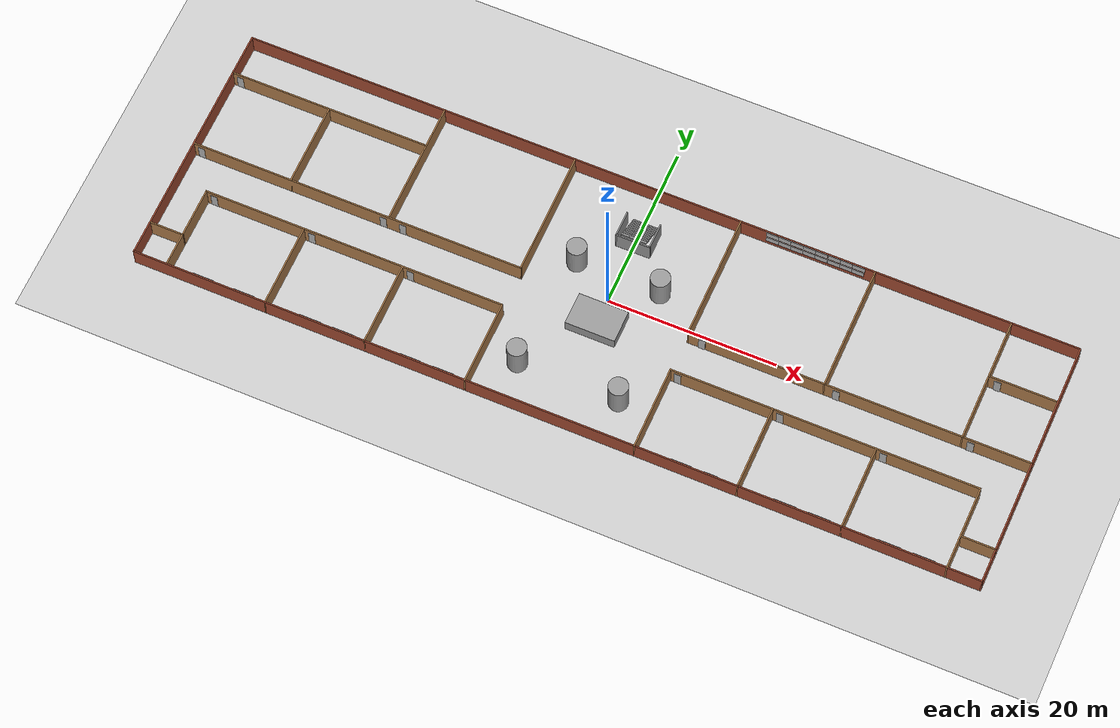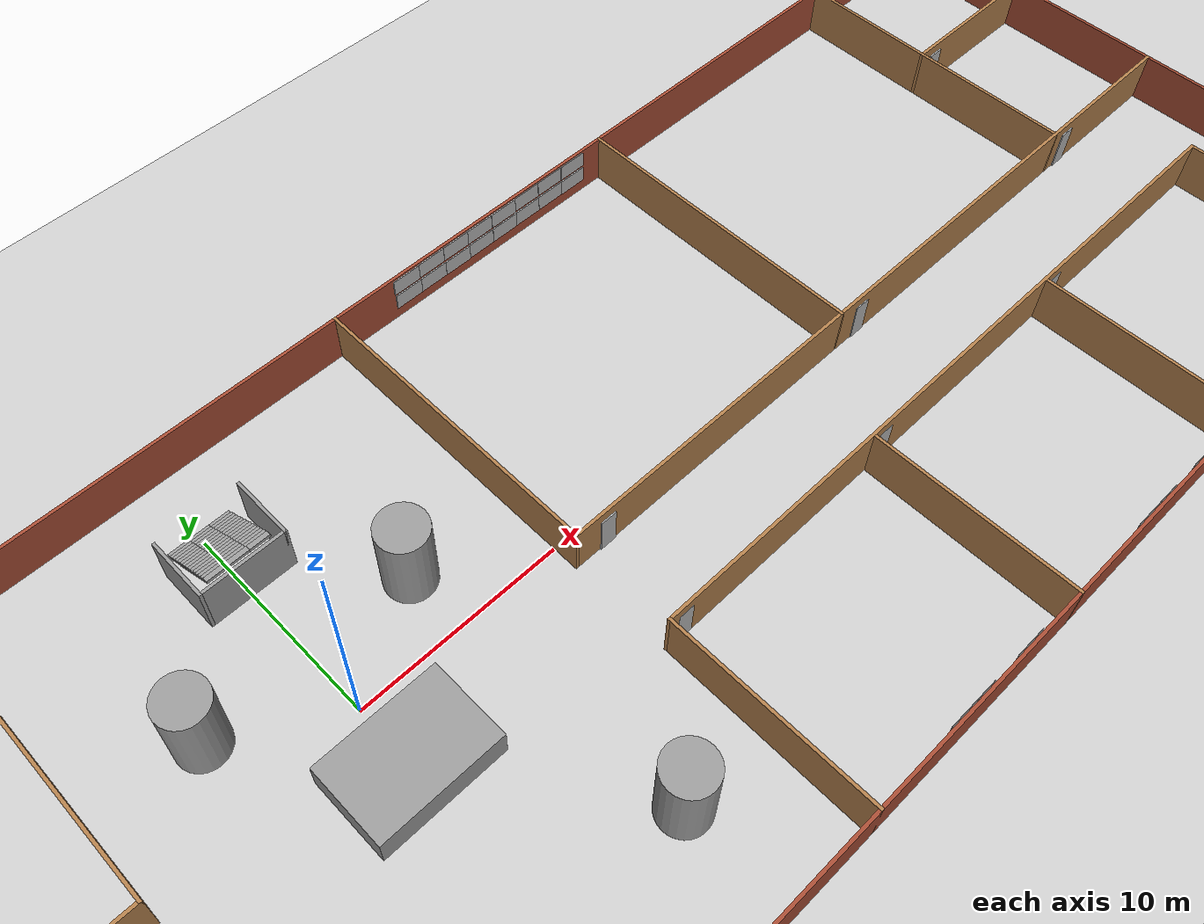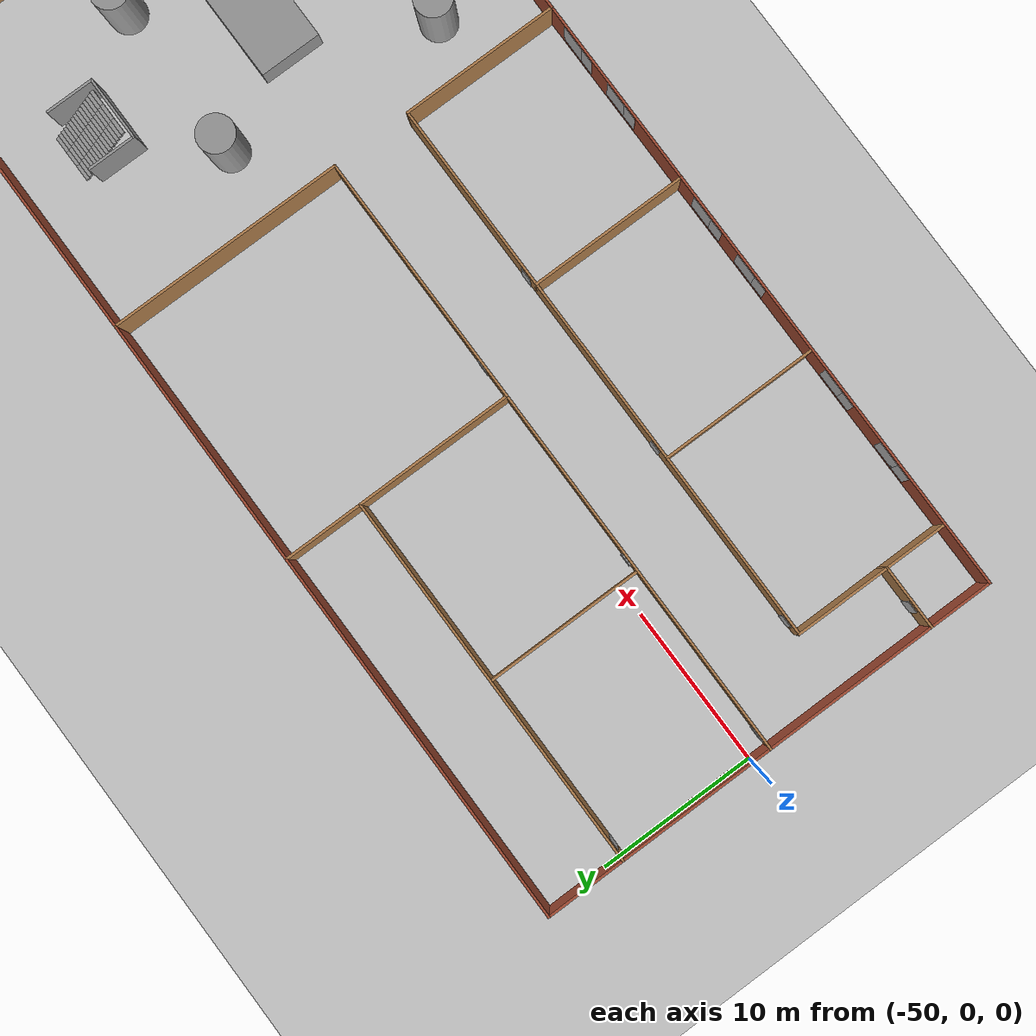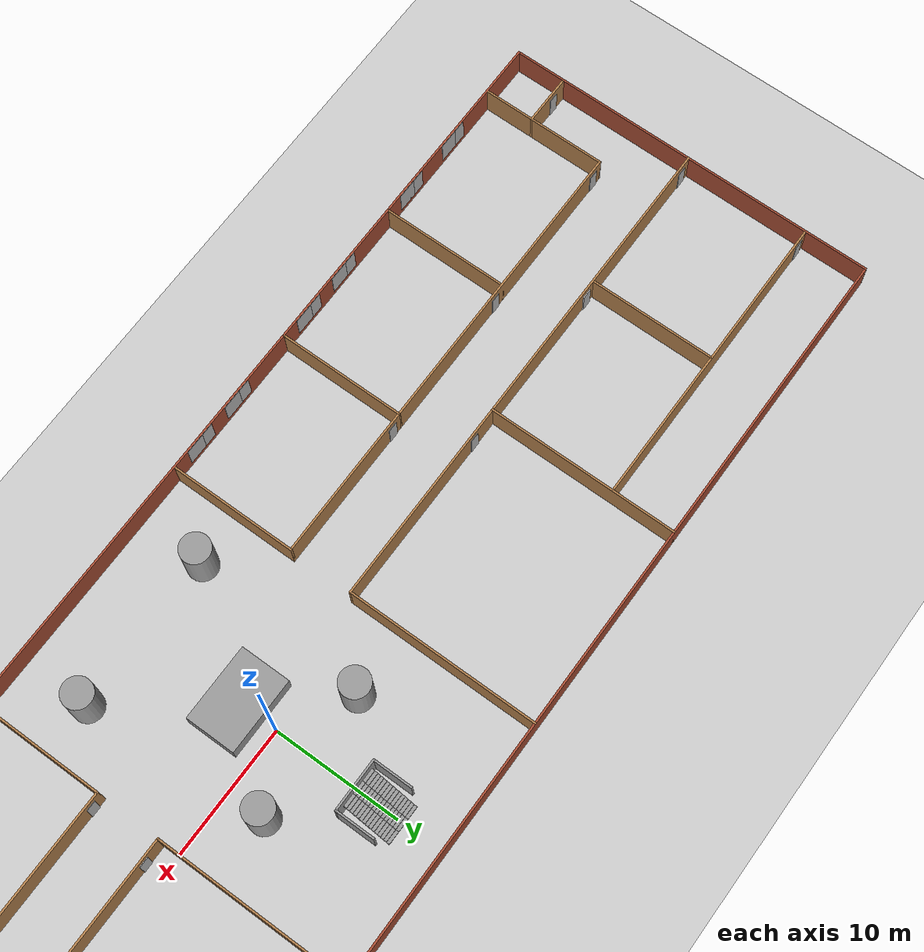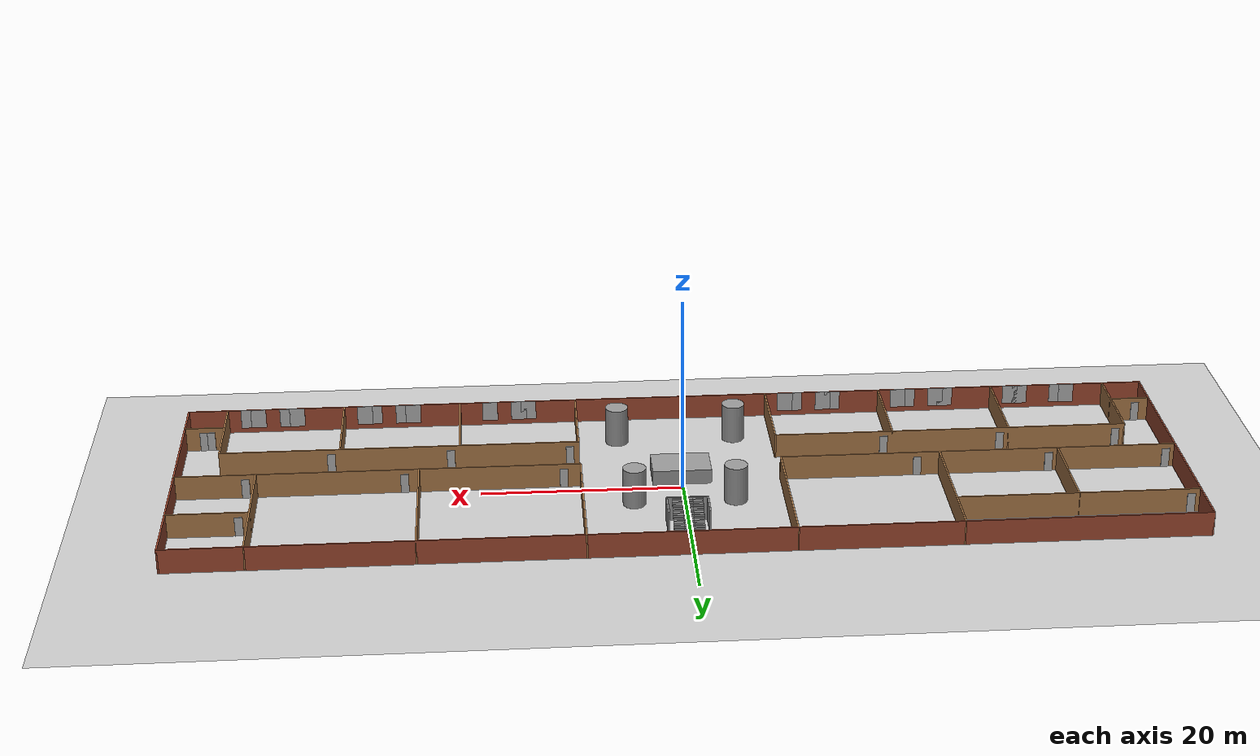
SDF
<sdf version="1.7">
 <world name="default">
  <light name="sun" type="directional">
   <pose>0 0 10 0 -0 0</pose>
   <diffuse>0.8 0.8 0.8 1</diffuse>
   <specular>0.2 0.2 0.2 1</specular>
   <attenuation>
    <range>1000</range>
    <constant>0.9</constant>
    <linear>0.01</linear>
    <quadratic>0.001</quadratic>
   </attenuation>
   <direction>-0.5 0.1 -0.9</direction>
   <spot><inner_angle>0</inner_angle><outer_angle>0</outer_angle><falloff>0</falloff></spot>
  </light>
  <model name="ground_plane">
   <static>1</static>
   <link name="link">
    <collision name="collision">
     <geometry><plane><normal>0 0 1</normal><size>100 100</size></plane></geometry>
     <surface>
      <contact><collide_bitmask>65535</collide_bitmask></contact>
      <friction><ode><mu>100</mu><mu2>50</mu2></ode></friction>
     </surface>
    </collision>
    <visual name="visual">
     <cast_shadows>0</cast_shadows>
     <geometry><plane><normal>0 0 1</normal><size>100 100</size></plane></geometry>
     <material>
      <script><uri>file://media/materials/scripts/gazebo.material</uri><name>Gazebo/Grey</name></script>
     </material>
    </visual>
   </link>
  </model>
  <gravity>0 0 -9.8</gravity>
  <magnetic_field>6e-06 2.3e-05 -4.2e-05</magnetic_field>
  <atmosphere type="adiabatic"/>
  <physics type="ode">
   <max_step_size>0.001</max_step_size>
   <real_time_factor>1</real_time_factor>
   <real_time_update_rate>1000</real_time_update_rate>
  </physics>
  <scene><ambient>0.4 0.4 0.4 1</ambient><background>0.7 0.7 0.7 1</background><shadows>1</shadows></scene>
  <audio><device>default</device></audio>
  <spherical_coordinates>
   <surface_model>EARTH_WGS84</surface_model>
   <latitude_deg>0</latitude_deg>
   <longitude_deg>0</longitude_deg>
   <elevation>0</elevation>
   <heading_deg>0</heading_deg>
  </spherical_coordinates>
  <model name="school_0910">
   <pose>0.103713 -1.21802 0 0 -0 0</pose>
   <link name="Stairs_0">
    <visual name="Stairs_0_Visual_0">
     <pose>0 11.6333 0.083333 0 -0 0</pose>
     <geometry><box><size>1 0.233333 0.166667</size></box></geometry>
     <material>
      <script><uri>file://media/materials/scripts/gazebo.material</uri><name>Gazebo/Grey</name></script>
      <ambient>1 1 1 1</ambient>
     </material>
     <meta><layer>0</layer></meta>
    </visual>
    <collision name="Stairs_0_Collision_0">
     <geometry><box><size>1 0.233333 0.166667</size></box></geometry>
     <pose>0 11.6333 0.083333 0 -0 0</pose>
    </collision>
    <visual name="Stairs_0_Visual_1">
     <pose>0 11.4 0.25 0 -0 0</pose>
     <geometry><box><size>1 0.233333 0.166667</size></box></geometry>
     <material>
      <script><uri>file://media/materials/scripts/gazebo.material</uri><name>Gazebo/Grey</name></script>
      <ambient>1 1 1 1</ambient>
     </material>
     <meta><layer>0</layer></meta>
    </visual>
    <collision name="Stairs_0_Collision_1">
     <geometry><box><size>1 0.233333 0.166667</size></box></geometry>
     <pose>0 11.4 0.25 0 -0 0</pose>
    </collision>
    <visual name="Stairs_0_Visual_2">
     <pose>0 11.1667 0.416667 0 -0 0</pose>
     <geometry><box><size>1 0.233333 0.166667</size></box></geometry>
     <material>
      <script><uri>file://media/materials/scripts/gazebo.material</uri><name>Gazebo/Grey</name></script>
      <ambient>1 1 1 1</ambient>
     </material>
     <meta><layer>0</layer></meta>
    </visual>
    <collision name="Stairs_0_Collision_2">
     <geometry><box><size>1 0.233333 0.166667</size></box></geometry>
     <pose>0 11.1667 0.416667 0 -0 0</pose>
    </collision>
    <visual name="Stairs_0_Visual_3">
     <pose>0 10.9333 0.583333 0 -0 0</pose>
     <geometry><box><size>1 0.233333 0.166667</size></box></geometry>
     <material>
      <script><uri>file://media/materials/scripts/gazebo.material</uri><name>Gazebo/Grey</name></script>
      <ambient>1 1 1 1</ambient>
     </material>
     <meta><layer>0</layer></meta>
    </visual>
    <collision name="Stairs_0_Collision_3">
     <geometry><box><size>1 0.233333 0.166667</size></box></geometry>
     <pose>0 10.9333 0.583333 0 -0 0</pose>
    </collision>
    <visual name="Stairs_0_Visual_4">
     <pose>0 10.7 0.75 0 -0 0</pose>
     <geometry><box><size>1 0.233333 0.166667</size></box></geometry>
     <material>
      <script><uri>file://media/materials/scripts/gazebo.material</uri><name>Gazebo/Grey</name></script>
      <ambient>1 1 1 1</ambient>
     </material>
     <meta><layer>0</layer></meta>
    </visual>
    <collision name="Stairs_0_Collision_4">
     <geometry><box><size>1 0.233333 0.166667</size></box></geometry>
     <pose>0 10.7 0.75 0 -0 0</pose>
    </collision>
    <visual name="Stairs_0_Visual_5">
     <pose>0 10.4667 0.916667 0 -0 0</pose>
     <geometry><box><size>1 0.233333 0.166667</size></box></geometry>
     <material>
      <script><uri>file://media/materials/scripts/gazebo.material</uri><name>Gazebo/Grey</name></script>
      <ambient>1 1 1 1</ambient>
     </material>
     <meta><layer>0</layer></meta>
    </visual>
    <collision name="Stairs_0_Collision_5">
     <geometry><box><size>1 0.233333 0.166667</size></box></geometry>
     <pose>0 10.4667 0.916667 0 -0 0</pose>
    </collision>
    <visual name="Stairs_0_Visual_6">
     <pose>0 10.2333 1.08333 0 -0 0</pose>
     <geometry><box><size>1 0.233333 0.166667</size></box></geometry>
     <material>
      <script><uri>file://media/materials/scripts/gazebo.material</uri><name>Gazebo/Grey</name></script>
      <ambient>1 1 1 1</ambient>
     </material>
     <meta><layer>0</layer></meta>
    </visual>
    <collision name="Stairs_0_Collision_6">
     <geometry><box><size>1 0.233333 0.166667</size></box></geometry>
     <pose>0 10.2333 1.08333 0 -0 0</pose>
    </collision>
    <visual name="Stairs_0_Visual_7">
     <pose>0 10 1.25 0 -0 0</pose>
     <geometry><box><size>1 0.233333 0.166667</size></box></geometry>
     <material>
      <script><uri>file://media/materials/scripts/gazebo.material</uri><name>Gazebo/Grey</name></script>
      <ambient>1 1 1 1</ambient>
     </material>
     <meta><layer>0</layer></meta>
    </visual>
    <collision name="Stairs_0_Collision_7">
     <geometry><box><size>1 0.233333 0.166667</size></box></geometry>
     <pose>0 10 1.25 0 -0 0</pose>
    </collision>
    <visual name="Stairs_0_Visual_8">
     <pose>0 9.76667 1.41667 0 -0 0</pose>
     <geometry><box><size>1 0.233333 0.166667</size></box></geometry>
     <material>
      <script><uri>file://media/materials/scripts/gazebo.material</uri><name>Gazebo/Grey</name></script>
      <ambient>1 1 1 1</ambient>
     </material>
     <meta><layer>0</layer></meta>
    </visual>
    <collision name="Stairs_0_Collision_8">
     <geometry><box><size>1 0.233333 0.166667</size></box></geometry>
     <pose>0 9.76667 1.41667 0 -0 0</pose>
    </collision>
    <visual name="Stairs_0_Visual_9">
     <pose>0 9.53333 1.58333 0 -0 0</pose>
     <geometry><box><size>1 0.233333 0.166667</size></box></geometry>
     <material>
      <script><uri>file://media/materials/scripts/gazebo.material</uri><name>Gazebo/Grey</name></script>
      <ambient>1 1 1 1</ambient>
     </material>
     <meta><layer>0</layer></meta>
    </visual>
    <collision name="Stairs_0_Collision_9">
     <geometry><box><size>1 0.233333 0.166667</size></box></geometry>
     <pose>0 9.53333 1.58333 0 -0 0</pose>
    </collision>
    <visual name="Stairs_0_Visual_10">
     <pose>0 9.3 1.75 0 -0 0</pose>
     <geometry><box><size>1 0.233333 0.166667</size></box></geometry>
     <material>
      <script><uri>file://media/materials/scripts/gazebo.material</uri><name>Gazebo/Grey</name></script>
      <ambient>1 1 1 1</ambient>
     </material>
     <meta><layer>0</layer></meta>
    </visual>
    <collision name="Stairs_0_Collision_10">
     <geometry><box><size>1 0.233333 0.166667</size></box></geometry>
     <pose>0 9.3 1.75 0 -0 0</pose>
    </collision>
    <visual name="Stairs_0_Visual_11">
     <pose>0 9.06667 1.91667 0 -0 0</pose>
     <geometry><box><size>1 0.233333 0.166667</size></box></geometry>
     <material>
      <script><uri>file://media/materials/scripts/gazebo.material</uri><name>Gazebo/Grey</name></script>
      <ambient>1 1 1 1</ambient>
     </material>
     <meta><layer>0</layer></meta>
    </visual>
    <collision name="Stairs_0_Collision_11">
     <geometry><box><size>1 0.233333 0.166667</size></box></geometry>
     <pose>0 9.06667 1.91667 0 -0 0</pose>
    </collision>
    <visual name="Stairs_0_Visual_12">
     <pose>0 8.83333 2.08333 0 -0 0</pose>
     <geometry><box><size>1 0.233333 0.166667</size></box></geometry>
     <material>
      <script><uri>file://media/materials/scripts/gazebo.material</uri><name>Gazebo/Grey</name></script>
      <ambient>1 1 1 1</ambient>
     </material>
     <meta><layer>0</layer></meta>
    </visual>
    <collision name="Stairs_0_Collision_12">
     <geometry><box><size>1 0.233333 0.166667</size></box></geometry>
     <pose>0 8.83333 2.08333 0 -0 0</pose>
    </collision>
    <visual name="Stairs_0_Visual_13">
     <pose>0 8.6 2.25 0 -0 0</pose>
     <geometry><box><size>1 0.233333 0.166667</size></box></geometry>
     <material>
      <script><uri>file://media/materials/scripts/gazebo.material</uri><name>Gazebo/Grey</name></script>
      <ambient>1 1 1 1</ambient>
     </material>
     <meta><layer>0</layer></meta>
    </visual>
    <collision name="Stairs_0_Collision_13">
     <geometry><box><size>1 0.233333 0.166667</size></box></geometry>
     <pose>0 8.6 2.25 0 -0 0</pose>
    </collision>
    <visual name="Stairs_0_Visual_14">
     <pose>0 8.36667 2.41667 0 -0 0</pose>
     <geometry><box><size>1 0.233333 0.166667</size></box></geometry>
     <material>
      <script><uri>file://media/materials/scripts/gazebo.material</uri><name>Gazebo/Grey</name></script>
      <ambient>1 1 1 1</ambient>
     </material>
     <meta><layer>0</layer></meta>
    </visual>
    <collision name="Stairs_0_Collision_14">
     <geometry><box><size>1 0.233333 0.166667</size></box></geometry>
     <pose>0 8.36667 2.41667 0 -0 0</pose>
    </collision>
   </link>
   <link name="Stairs_1">
    <visual name="Stairs_1_Visual_0">
     <pose>-1 11.6333 0.083333 0 -0 0</pose>
     <geometry><box><size>1 0.233333 0.166667</size></box></geometry>
     <material>
      <script><uri>file://media/materials/scripts/gazebo.material</uri><name>Gazebo/Grey</name></script>
      <ambient>1 1 1 1</ambient>
     </material>
     <meta><layer>0</layer></meta>
    </visual>
    <collision name="Stairs_1_Collision_0">
     <geometry><box><size>1 0.233333 0.166667</size></box></geometry>
     <pose>-1 11.6333 0.083333 0 -0 0</pose>
    </collision>
    <visual name="Stairs_1_Visual_1">
     <pose>-1 11.4 0.25 0 -0 0</pose>
     <geometry><box><size>1 0.233333 0.166667</size></box></geometry>
     <material>
      <script><uri>file://media/materials/scripts/gazebo.material</uri><name>Gazebo/Grey</name></script>
      <ambient>1 1 1 1</ambient>
     </material>
     <meta><layer>0</layer></meta>
    </visual>
    <collision name="Stairs_1_Collision_1">
     <geometry><box><size>1 0.233333 0.166667</size></box></geometry>
     <pose>-1 11.4 0.25 0 -0 0</pose>
    </collision>
    <visual name="Stairs_1_Visual_2">
     <pose>-1 11.1667 0.416667 0 -0 0</pose>
     <geometry><box><size>1 0.233333 0.166667</size></box></geometry>
     <material>
      <script><uri>file://media/materials/scripts/gazebo.material</uri><name>Gazebo/Grey</name></script>
      <ambient>1 1 1 1</ambient>
     </material>
     <meta><layer>0</layer></meta>
    </visual>
    <collision name="Stairs_1_Collision_2">
     <geometry><box><size>1 0.233333 0.166667</size></box></geometry>
     <pose>-1 11.1667 0.416667 0 -0 0</pose>
    </collision>
    <visual name="Stairs_1_Visual_3">
     <pose>-1 10.9333 0.583333 0 -0 0</pose>
     <geometry><box><size>1 0.233333 0.166667</size></box></geometry>
     <material>
      <script><uri>file://media/materials/scripts/gazebo.material</uri><name>Gazebo/Grey</name></script>
      <ambient>1 1 1 1</ambient>
     </material>
     <meta><layer>0</layer></meta>
    </visual>
    <collision name="Stairs_1_Collision_3">
     <geometry><box><size>1 0.233333 0.166667</size></box></geometry>
     <pose>-1 10.9333 0.583333 0 -0 0</pose>
    </collision>
    <visual name="Stairs_1_Visual_4">
     <pose>-1 10.7 0.75 0 -0 0</pose>
     <geometry><box><size>1 0.233333 0.166667</size></box></geometry>
     <material>
      <script><uri>file://media/materials/scripts/gazebo.material</uri><name>Gazebo/Grey</name></script>
      <ambient>1 1 1 1</ambient>
     </material>
     <meta><layer>0</layer></meta>
    </visual>
    <collision name="Stairs_1_Collision_4">
     <geometry><box><size>1 0.233333 0.166667</size></box></geometry>
     <pose>-1 10.7 0.75 0 -0 0</pose>
    </collision>
    <visual name="Stairs_1_Visual_5">
     <pose>-1 10.4667 0.916667 0 -0 0</pose>
     <geometry><box><size>1 0.233333 0.166667</size></box></geometry>
     <material>
      <script><uri>file://media/materials/scripts/gazebo.material</uri><name>Gazebo/Grey</name></script>
      <ambient>1 1 1 1</ambient>
     </material>
     <meta><layer>0</layer></meta>
    </visual>
    <collision name="Stairs_1_Collision_5">
     <geometry><box><size>1 0.233333 0.166667</size></box></geometry>
     <pose>-1 10.4667 0.916667 0 -0 0</pose>
    </collision>
    <visual name="Stairs_1_Visual_6">
     <pose>-1 10.2333 1.08333 0 -0 0</pose>
     <geometry><box><size>1 0.233333 0.166667</size></box></geometry>
     <material>
      <script><uri>file://media/materials/scripts/gazebo.material</uri><name>Gazebo/Grey</name></script>
      <ambient>1 1 1 1</ambient>
     </material>
     <meta><layer>0</layer></meta>
    </visual>
    <collision name="Stairs_1_Collision_6">
     <geometry><box><size>1 0.233333 0.166667</size></box></geometry>
     <pose>-1 10.2333 1.08333 0 -0 0</pose>
    </collision>
    <visual name="Stairs_1_Visual_7">
     <pose>-1 10 1.25 0 -0 0</pose>
     <geometry><box><size>1 0.233333 0.166667</size></box></geometry>
     <material>
      <script><uri>file://media/materials/scripts/gazebo.material</uri><name>Gazebo/Grey</name></script>
      <ambient>1 1 1 1</ambient>
     </material>
     <meta><layer>0</layer></meta>
    </visual>
    <collision name="Stairs_1_Collision_7">
     <geometry><box><size>1 0.233333 0.166667</size></box></geometry>
     <pose>-1 10 1.25 0 -0 0</pose>
    </collision>
    <visual name="Stairs_1_Visual_8">
     <pose>-1 9.76667 1.41667 0 -0 0</pose>
     <geometry><box><size>1 0.233333 0.166667</size></box></geometry>
     <material>
      <script><uri>file://media/materials/scripts/gazebo.material</uri><name>Gazebo/Grey</name></script>
      <ambient>1 1 1 1</ambient>
     </material>
     <meta><layer>0</layer></meta>
    </visual>
    <collision name="Stairs_1_Collision_8">
     <geometry><box><size>1 0.233333 0.166667</size></box></geometry>
     <pose>-1 9.76667 1.41667 0 -0 0</pose>
    </collision>
    <visual name="Stairs_1_Visual_9">
     <pose>-1 9.53333 1.58333 0 -0 0</pose>
     <geometry><box><size>1 0.233333 0.166667</size></box></geometry>
     <material>
      <script><uri>file://media/materials/scripts/gazebo.material</uri><name>Gazebo/Grey</name></script>
      <ambient>1 1 1 1</ambient>
     </material>
     <meta><layer>0</layer></meta>
    </visual>
    <collision name="Stairs_1_Collision_9">
     <geometry><box><size>1 0.233333 0.166667</size></box></geometry>
     <pose>-1 9.53333 1.58333 0 -0 0</pose>
    </collision>
    <visual name="Stairs_1_Visual_10">
     <pose>-1 9.3 1.75 0 -0 0</pose>
     <geometry><box><size>1 0.233333 0.166667</size></box></geometry>
     <material>
      <script><uri>file://media/materials/scripts/gazebo.material</uri><name>Gazebo/Grey</name></script>
      <ambient>1 1 1 1</ambient>
     </material>
     <meta><layer>0</layer></meta>
    </visual>
    <collision name="Stairs_1_Collision_10">
     <geometry><box><size>1 0.233333 0.166667</size></box></geometry>
     <pose>-1 9.3 1.75 0 -0 0</pose>
    </collision>
    <visual name="Stairs_1_Visual_11">
     <pose>-1 9.06667 1.91667 0 -0 0</pose>
     <geometry><box><size>1 0.233333 0.166667</size></box></geometry>
     <material>
      <script><uri>file://media/materials/scripts/gazebo.material</uri><name>Gazebo/Grey</name></script>
      <ambient>1 1 1 1</ambient>
     </material>
     <meta><layer>0</layer></meta>
    </visual>
    <collision name="Stairs_1_Collision_11">
     <geometry><box><size>1 0.233333 0.166667</size></box></geometry>
     <pose>-1 9.06667 1.91667 0 -0 0</pose>
    </collision>
    <visual name="Stairs_1_Visual_12">
     <pose>-1 8.83333 2.08333 0 -0 0</pose>
     <geometry><box><size>1 0.233333 0.166667</size></box></geometry>
     <material>
      <script><uri>file://media/materials/scripts/gazebo.material</uri><name>Gazebo/Grey</name></script>
      <ambient>1 1 1 1</ambient>
     </material>
     <meta><layer>0</layer></meta>
    </visual>
    <collision name="Stairs_1_Collision_12">
     <geometry><box><size>1 0.233333 0.166667</size></box></geometry>
     <pose>-1 8.83333 2.08333 0 -0 0</pose>
    </collision>
    <visual name="Stairs_1_Visual_13">
     <pose>-1 8.6 2.25 0 -0 0</pose>
     <geometry><box><size>1 0.233333 0.166667</size></box></geometry>
     <material>
      <script><uri>file://media/materials/scripts/gazebo.material</uri><name>Gazebo/Grey</name></script>
      <ambient>1 1 1 1</ambient>
     </material>
     <meta><layer>0</layer></meta>
    </visual>
    <collision name="Stairs_1_Collision_13">
     <geometry><box><size>1 0.233333 0.166667</size></box></geometry>
     <pose>-1 8.6 2.25 0 -0 0</pose>
    </collision>
    <visual name="Stairs_1_Visual_14">
     <pose>-1 8.36667 2.41667 0 -0 0</pose>
     <geometry><box><size>1 0.233333 0.166667</size></box></geometry>
     <material>
      <script><uri>file://media/materials/scripts/gazebo.material</uri><name>Gazebo/Grey</name></script>
      <ambient>1 1 1 1</ambient>
     </material>
     <meta><layer>0</layer></meta>
    </visual>
    <collision name="Stairs_1_Collision_14">
     <geometry><box><size>1 0.233333 0.166667</size></box></geometry>
     <pose>-1 8.36667 2.41667 0 -0 0</pose>
    </collision>
   </link>
   <link name="Stairs_2">
    <visual name="Stairs_2_Visual_0">
     <pose>1 11.6333 0.083333 0 -0 0</pose>
     <geometry><box><size>1 0.233333 0.166667</size></box></geometry>
     <material>
      <script><uri>file://media/materials/scripts/gazebo.material</uri><name>Gazebo/Grey</name></script>
      <ambient>1 1 1 1</ambient>
     </material>
     <meta><layer>0</layer></meta>
    </visual>
    <collision name="Stairs_2_Collision_0">
     <geometry><box><size>1 0.233333 0.166667</size></box></geometry>
     <pose>1 11.6333 0.083333 0 -0 0</pose>
    </collision>
    <visual name="Stairs_2_Visual_1">
     <pose>1 11.4 0.25 0 -0 0</pose>
     <geometry><box><size>1 0.233333 0.166667</size></box></geometry>
     <material>
      <script><uri>file://media/materials/scripts/gazebo.material</uri><name>Gazebo/Grey</name></script>
      <ambient>1 1 1 1</ambient>
     </material>
     <meta><layer>0</layer></meta>
    </visual>
    <collision name="Stairs_2_Collision_1">
     <geometry><box><size>1 0.233333 0.166667</size></box></geometry>
     <pose>1 11.4 0.25 0 -0 0</pose>
    </collision>
    <visual name="Stairs_2_Visual_2">
     <pose>1 11.1667 0.416667 0 -0 0</pose>
     <geometry><box><size>1 0.233333 0.166667</size></box></geometry>
     <material>
      <script><uri>file://media/materials/scripts/gazebo.material</uri><name>Gazebo/Grey</name></script>
      <ambient>1 1 1 1</ambient>
     </material>
     <meta><layer>0</layer></meta>
    </visual>
    <collision name="Stairs_2_Collision_2">
     <geometry><box><size>1 0.233333 0.166667</size></box></geometry>
     <pose>1 11.1667 0.416667 0 -0 0</pose>
    </collision>
    <visual name="Stairs_2_Visual_3">
     <pose>1 10.9333 0.583333 0 -0 0</pose>
     <geometry><box><size>1 0.233333 0.166667</size></box></geometry>
     <material>
      <script><uri>file://media/materials/scripts/gazebo.material</uri><name>Gazebo/Grey</name></script>
      <ambient>1 1 1 1</ambient>
     </material>
     <meta><layer>0</layer></meta>
    </visual>
    <collision name="Stairs_2_Collision_3">
     <geometry><box><size>1 0.233333 0.166667</size></box></geometry>
     <pose>1 10.9333 0.583333 0 -0 0</pose>
    </collision>
    <visual name="Stairs_2_Visual_4">
     <pose>1 10.7 0.75 0 -0 0</pose>
     <geometry><box><size>1 0.233333 0.166667</size></box></geometry>
     <material>
      <script><uri>file://media/materials/scripts/gazebo.material</uri><name>Gazebo/Grey</name></script>
      <ambient>1 1 1 1</ambient>
     </material>
     <meta><layer>0</layer></meta>
    </visual>
    <collision name="Stairs_2_Collision_4">
     <geometry><box><size>1 0.233333 0.166667</size></box></geometry>
     <pose>1 10.7 0.75 0 -0 0</pose>
    </collision>
    <visual name="Stairs_2_Visual_5">
     <pose>1 10.4667 0.916667 0 -0 0</pose>
     <geometry><box><size>1 0.233333 0.166667</size></box></geometry>
     <material>
      <script><uri>file://media/materials/scripts/gazebo.material</uri><name>Gazebo/Grey</name></script>
      <ambient>1 1 1 1</ambient>
     </material>
     <meta><layer>0</layer></meta>
    </visual>
    <collision name="Stairs_2_Collision_5">
     <geometry><box><size>1 0.233333 0.166667</size></box></geometry>
     <pose>1 10.4667 0.916667 0 -0 0</pose>
    </collision>
    <visual name="Stairs_2_Visual_6">
     <pose>1 10.2333 1.08333 0 -0 0</pose>
     <geometry><box><size>1 0.233333 0.166667</size></box></geometry>
     <material>
      <script><uri>file://media/materials/scripts/gazebo.material</uri><name>Gazebo/Grey</name></script>
      <ambient>1 1 1 1</ambient>
     </material>
     <meta><layer>0</layer></meta>
    </visual>
    <collision name="Stairs_2_Collision_6">
     <geometry><box><size>1 0.233333 0.166667</size></box></geometry>
     <pose>1 10.2333 1.08333 0 -0 0</pose>
    </collision>
    <visual name="Stairs_2_Visual_7">
     <pose>1 10 1.25 0 -0 0</pose>
     <geometry><box><size>1 0.233333 0.166667</size></box></geometry>
     <material>
      <script><uri>file://media/materials/scripts/gazebo.material</uri><name>Gazebo/Grey</name></script>
      <ambient>1 1 1 1</ambient>
     </material>
     <meta><layer>0</layer></meta>
    </visual>
    <collision name="Stairs_2_Collision_7">
     <geometry><box><size>1 0.233333 0.166667</size></box></geometry>
     <pose>1 10 1.25 0 -0 0</pose>
    </collision>
    <visual name="Stairs_2_Visual_8">
     <pose>1 9.76667 1.41667 0 -0 0</pose>
     <geometry><box><size>1 0.233333 0.166667</size></box></geometry>
     <material>
      <script><uri>file://media/materials/scripts/gazebo.material</uri><name>Gazebo/Grey</name></script>
      <ambient>1 1 1 1</ambient>
     </material>
     <meta><layer>0</layer></meta>
    </visual>
    <collision name="Stairs_2_Collision_8">
     <geometry><box><size>1 0.233333 0.166667</size></box></geometry>
     <pose>1 9.76667 1.41667 0 -0 0</pose>
    </collision>
    <visual name="Stairs_2_Visual_9">
     <pose>1 9.53333 1.58333 0 -0 0</pose>
     <geometry><box><size>1 0.233333 0.166667</size></box></geometry>
     <material>
      <script><uri>file://media/materials/scripts/gazebo.material</uri><name>Gazebo/Grey</name></script>
      <ambient>1 1 1 1</ambient>
     </material>
     <meta><layer>0</layer></meta>
    </visual>
    <collision name="Stairs_2_Collision_9">
     <geometry><box><size>1 0.233333 0.166667</size></box></geometry>
     <pose>1 9.53333 1.58333 0 -0 0</pose>
    </collision>
    <visual name="Stairs_2_Visual_10">
     <pose>1 9.3 1.75 0 -0 0</pose>
     <geometry><box><size>1 0.233333 0.166667</size></box></geometry>
     <material>
      <script><uri>file://media/materials/scripts/gazebo.material</uri><name>Gazebo/Grey</name></script>
      <ambient>1 1 1 1</ambient>
     </material>
     <meta><layer>0</layer></meta>
    </visual>
    <collision name="Stairs_2_Collision_10">
     <geometry><box><size>1 0.233333 0.166667</size></box></geometry>
     <pose>1 9.3 1.75 0 -0 0</pose>
    </collision>
    <visual name="Stairs_2_Visual_11">
     <pose>1 9.06667 1.91667 0 -0 0</pose>
     <geometry><box><size>1 0.233333 0.166667</size></box></geometry>
     <material>
      <script><uri>file://media/materials/scripts/gazebo.material</uri><name>Gazebo/Grey</name></script>
      <ambient>1 1 1 1</ambient>
     </material>
     <meta><layer>0</layer></meta>
    </visual>
    <collision name="Stairs_2_Collision_11">
     <geometry><box><size>1 0.233333 0.166667</size></box></geometry>
     <pose>1 9.06667 1.91667 0 -0 0</pose>
    </collision>
    <visual name="Stairs_2_Visual_12">
     <pose>1 8.83333 2.08333 0 -0 0</pose>
     <geometry><box><size>1 0.233333 0.166667</size></box></geometry>
     <material>
      <script><uri>file://media/materials/scripts/gazebo.material</uri><name>Gazebo/Grey</name></script>
      <ambient>1 1 1 1</ambient>
     </material>
     <meta><layer>0</layer></meta>
    </visual>
    <collision name="Stairs_2_Collision_12">
     <geometry><box><size>1 0.233333 0.166667</size></box></geometry>
     <pose>1 8.83333 2.08333 0 -0 0</pose>
    </collision>
    <visual name="Stairs_2_Visual_13">
     <pose>1 8.6 2.25 0 -0 0</pose>
     <geometry><box><size>1 0.233333 0.166667</size></box></geometry>
     <material>
      <script><uri>file://media/materials/scripts/gazebo.material</uri><name>Gazebo/Grey</name></script>
      <ambient>1 1 1 1</ambient>
     </material>
     <meta><layer>0</layer></meta>
    </visual>
    <collision name="Stairs_2_Collision_13">
     <geometry><box><size>1 0.233333 0.166667</size></box></geometry>
     <pose>1 8.6 2.25 0 -0 0</pose>
    </collision>
    <visual name="Stairs_2_Visual_14">
     <pose>1 8.36667 2.41667 0 -0 0</pose>
     <geometry><box><size>1 0.233333 0.166667</size></box></geometry>
     <material>
      <script><uri>file://media/materials/scripts/gazebo.material</uri><name>Gazebo/Grey</name></script>
      <ambient>1 1 1 1</ambient>
     </material>
     <meta><layer>0</layer></meta>
    </visual>
    <collision name="Stairs_2_Collision_14">
     <geometry><box><size>1 0.233333 0.166667</size></box></geometry>
     <pose>1 8.36667 2.41667 0 -0 0</pose>
    </collision>
   </link>
   <link name="Wall_15">
    <collision name="Wall_15_Collision">
     <geometry><box><size>30.15 0.15 2.5</size></box></geometry>
     <pose>0 0 1.25 0 -0 0</pose>
    </collision>
    <visual name="Wall_15_Visual">
     <pose>0 0 1.25 0 -0 0</pose>
     <geometry><box><size>30.15 0.15 2.5</size></box></geometry>
     <material>
      <script><uri>file://media/materials/scripts/gazebo.material</uri><name>Gazebo/Bricks</name></script>
      <ambient>1 1 1 1</ambient>
     </material>
     <meta><layer>0</layer></meta>
    </visual>
    <pose>-50 0 0 0 -0 -1.5708</pose>
   </link>
   <link name="Wall_17">
    <collision name="Wall_17_Collision">
     <geometry><box><size>100.15 0.15 2.5</size></box></geometry>
     <pose>0 0 1.25 0 -0 0</pose>
    </collision>
    <visual name="Wall_17_Visual">
     <pose>0 0 1.25 0 -0 0</pose>
     <geometry><box><size>100.15 0.15 2.5</size></box></geometry>
     <material>
      <script><uri>file://media/materials/scripts/gazebo.material</uri><name>Gazebo/Bricks</name></script>
      <ambient>1 1 1 1</ambient>
     </material>
     <meta><layer>0</layer></meta>
    </visual>
    <pose>0 -15 0 0 -0 0</pose>
   </link>
   <link name="Wall_19">
    <collision name="Wall_19_Collision">
     <geometry><box><size>30.15 0.15 2.5</size></box></geometry>
     <pose>0 0 1.25 0 -0 0</pose>
    </collision>
    <visual name="Wall_19_Visual">
     <pose>0 0 1.25 0 -0 0</pose>
     <geometry><box><size>30.15 0.15 2.5</size></box></geometry>
     <material>
      <script><uri>file://media/materials/scripts/gazebo.material</uri><name>Gazebo/Bricks</name></script>
      <ambient>1 1 1 1</ambient>
     </material>
     <meta><layer>0</layer></meta>
    </visual>
    <pose>50 0 0 0 -0 -1.5708</pose>
   </link>
   <link name="Wall_21">
    <collision name="Wall_21_Collision">
     <geometry><box><size>24.15 0.15 2.5</size></box></geometry>
     <pose>0 0 1.25 0 -0 0</pose>
    </collision>
    <visual name="Wall_21_Visual">
     <pose>0 0 1.25 0 -0 0</pose>
     <geometry><box><size>24.15 0.15 2.5</size></box></geometry>
     <material>
      <script><uri>file://media/materials/scripts/gazebo.material</uri><name>Gazebo/Wood</name></script>
      <ambient>1 1 1 1</ambient>
     </material>
     <meta><layer>0</layer></meta>
    </visual>
    <pose>-38 10 0 0 -0 0</pose>
   </link>
   <link name="Wall_23">
    <collision name="Wall_23_Collision">
     <geometry><box><size>10.15 0.15 2.5</size></box></geometry>
     <pose>0 0 1.25 0 -0 0</pose>
    </collision>
    <visual name="Wall_23_Visual">
     <pose>0 0 1.25 0 -0 0</pose>
     <geometry><box><size>10.15 0.15 2.5</size></box></geometry>
     <material>
      <script><uri>file://media/materials/scripts/gazebo.material</uri><name>Gazebo/Wood</name></script>
      <ambient>1 1 1 1</ambient>
     </material>
     <meta><layer>0</layer></meta>
    </visual>
    <pose>-38 5 0 0 -0 -1.5708</pose>
   </link>
   <link name="Wall_25">
    <collision name="Wall_25_Collision">
     <geometry><box><size>15.15 0.15 2.5</size></box></geometry>
     <pose>0 0 1.25 0 -0 0</pose>
    </collision>
    <visual name="Wall_25_Visual">
     <pose>0 0 1.25 0 -0 0</pose>
     <geometry><box><size>15.15 0.15 2.5</size></box></geometry>
     <material>
      <script><uri>file://media/materials/scripts/gazebo.material</uri><name>Gazebo/Wood</name></script>
      <ambient>1 1 1 1</ambient>
     </material>
     <meta><layer>0</layer></meta>
    </visual>
    <pose>-26 7.5 0 0 -0 -1.5708</pose>
   </link>
   <link name="Wall_27">
    <collision name="Wall_27_Collision">
     <geometry><box><size>40.15 0.15 2.5</size></box></geometry>
     <pose>0 0 1.25 0 -0 0</pose>
    </collision>
    <visual name="Wall_27_Visual">
     <pose>0 0 1.25 0 -0 0</pose>
     <geometry><box><size>40.15 0.15 2.5</size></box></geometry>
     <material>
      <script><uri>file://media/materials/scripts/gazebo.material</uri><name>Gazebo/Wood</name></script>
      <ambient>1 1 1 1</ambient>
     </material>
     <meta><layer>0</layer></meta>
    </visual>
    <pose>-30 0 0 0 -0 0</pose>
   </link>
   <link name="Wall_29">
    <collision name="Wall_29_Collision">
     <geometry><box><size>15.15 0.15 2.5</size></box></geometry>
     <pose>0 0 1.25 0 -0 0</pose>
    </collision>
    <visual name="Wall_29_Visual">
     <pose>0 0 1.25 0 -0 0</pose>
     <geometry><box><size>15.15 0.15 2.5</size></box></geometry>
     <material>
      <script><uri>file://media/materials/scripts/gazebo.material</uri><name>Gazebo/Wood</name></script>
      <ambient>1 1 1 1</ambient>
     </material>
     <meta><layer>0</layer></meta>
    </visual>
    <pose>-10 7.5 0 0 -0 -1.5708</pose>
   </link>
   <link name="Wall_32">
    <collision name="Wall_32_Collision">
     <geometry><box><size>4.15 0.15 2.5</size></box></geometry>
     <pose>0 0 1.25 0 -0 0</pose>
    </collision>
    <visual name="Wall_32_Visual">
     <pose>0 0 1.25 0 -0 0</pose>
     <geometry><box><size>4.15 0.15 2.5</size></box></geometry>
     <material>
      <script><uri>file://media/materials/scripts/gazebo.material</uri><name>Gazebo/Wood</name></script>
      <ambient>1 1 1 1</ambient>
     </material>
     <meta><layer>0</layer></meta>
    </visual>
    <pose>-48 -11 0 0 -0 0</pose>
   </link>
   <link name="Wall_35">
    <collision name="Wall_35_Collision">
     <geometry><box><size>10.15 0.15 2.5</size></box></geometry>
     <pose>0 0 1.25 0 -0 0</pose>
    </collision>
    <visual name="Wall_35_Visual">
     <pose>0 0 1.25 0 -0 0</pose>
     <geometry><box><size>10.15 0.15 2.5</size></box></geometry>
     <material>
      <script><uri>file://media/materials/scripts/gazebo.material</uri><name>Gazebo/Wood</name></script>
      <ambient>1 1 1 1</ambient>
     </material>
     <meta><layer>0</layer></meta>
    </visual>
    <pose>-46 -10 0 0 -0 -1.5708</pose>
   </link>
   <link name="Wall_37">
    <collision name="Wall_37_Collision">
     <geometry><box><size>36.15 0.15 2.5</size></box></geometry>
     <pose>0 0 1.25 0 -0 0</pose>
    </collision>
    <visual name="Wall_37_Visual">
     <pose>0 0 1.25 0 -0 0</pose>
     <geometry><box><size>36.15 0.15 2.5</size></box></geometry>
     <material>
      <script><uri>file://media/materials/scripts/gazebo.material</uri><name>Gazebo/Wood</name></script>
      <ambient>1 1 1 1</ambient>
     </material>
     <meta><layer>0</layer></meta>
    </visual>
    <pose>-28 -5 0 0 -0 0</pose>
   </link>
   <link name="Wall_39">
    <collision name="Wall_39_Collision">
     <geometry><box><size>10.15 0.15 2.5</size></box></geometry>
     <pose>0 0 1.25 0 -0 0</pose>
    </collision>
    <visual name="Wall_39_Visual">
     <pose>0 0 1.25 0 -0 0</pose>
     <geometry><box><size>10.15 0.15 2.5</size></box></geometry>
     <material>
      <script><uri>file://media/materials/scripts/gazebo.material</uri><name>Gazebo/Wood</name></script>
      <ambient>1 1 1 1</ambient>
     </material>
     <meta><layer>0</layer></meta>
    </visual>
    <pose>-34 -10 0 0 -0 -1.5708</pose>
   </link>
   <link name="Wall_41">
    <collision name="Wall_41_Collision">
     <geometry><box><size>10.15 0.15 2.5</size></box></geometry>
     <pose>0 0 1.25 0 -0 0</pose>
    </collision>
    <visual name="Wall_41_Visual">
     <pose>0 0 1.25 0 -0 0</pose>
     <geometry><box><size>10.15 0.15 2.5</size></box></geometry>
     <material>
      <script><uri>file://media/materials/scripts/gazebo.material</uri><name>Gazebo/Wood</name></script>
      <ambient>1 1 1 1</ambient>
     </material>
     <meta><layer>0</layer></meta>
    </visual>
    <pose>-22 -10 0 0 -0 -1.5708</pose>
   </link>
   <link name="Wall_43">
    <collision name="Wall_43_Collision">
     <geometry><box><size>10.15 0.15 2.5</size></box></geometry>
     <pose>0 0 1.25 0 -0 0</pose>
    </collision>
    <visual name="Wall_43_Visual">
     <pose>0 0 1.25 0 -0 0</pose>
     <geometry><box><size>10.15 0.15 2.5</size></box></geometry>
     <material>
      <script><uri>file://media/materials/scripts/gazebo.material</uri><name>Gazebo/Wood</name></script>
      <ambient>1 1 1 1</ambient>
     </material>
     <meta><layer>0</layer></meta>
    </visual>
    <pose>-10 -10 0 0 -0 -1.5708</pose>
   </link>
   <link name="Wall_45">
    <collision name="Wall_45_Collision">
     <geometry><box><size>15.15 0.15 2.5</size></box></geometry>
     <pose>0 0 1.25 0 -0 0</pose>
    </collision>
    <visual name="Wall_45_Visual">
     <pose>0 0 1.25 0 -0 0</pose>
     <geometry><box><size>15.15 0.15 2.5</size></box></geometry>
     <material>
      <script><uri>file://media/materials/scripts/gazebo.material</uri><name>Gazebo/Wood</name></script>
      <ambient>1 1 1 1</ambient>
     </material>
     <meta><layer>0</layer></meta>
    </visual>
    <pose>26 7.5 0 0 -0 -1.5708</pose>
   </link>
   <link name="Wall_47">
    <collision name="Wall_47_Collision">
     <geometry><box><size>15.15 0.15 2.5</size></box></geometry>
     <pose>0 0 1.25 0 -0 0</pose>
    </collision>
    <visual name="Wall_47_Visual">
     <pose>0 0 1.25 0 -0 0</pose>
     <geometry><box><size>15.15 0.15 2.5</size></box></geometry>
     <material>
      <script><uri>file://media/materials/scripts/gazebo.material</uri><name>Gazebo/Wood</name></script>
      <ambient>1 1 1 1</ambient>
     </material>
     <meta><layer>0</layer></meta>
    </visual>
    <pose>42 7.5 0 0 -0 -1.5708</pose>
   </link>
   <link name="Wall_49">
    <collision name="Wall_49_Collision">
     <geometry><box><size>8.15 0.15 2.5</size></box></geometry>
     <pose>0 0 1.25 0 -0 0</pose>
    </collision>
    <visual name="Wall_49_Visual">
     <pose>0 0 1.25 0 -0 0</pose>
     <geometry><box><size>8.15 0.15 2.5</size></box></geometry>
     <material>
      <script><uri>file://media/materials/scripts/gazebo.material</uri><name>Gazebo/Wood</name></script>
      <ambient>1 1 1 1</ambient>
     </material>
     <meta><layer>0</layer></meta>
    </visual>
    <pose>46 8 0 0 -0 0</pose>
   </link>
   <link name="Wall_51">
    <collision name="Wall_51_Collision">
     <geometry><box><size>15.15 0.15 2.5</size></box></geometry>
     <pose>0 0 1.25 0 -0 0</pose>
    </collision>
    <visual name="Wall_51_Visual">
     <pose>0 0 1.25 0 -0 0</pose>
     <geometry><box><size>15.15 0.15 2.5</size></box></geometry>
     <material>
      <script><uri>file://media/materials/scripts/gazebo.material</uri><name>Gazebo/Wood</name></script>
      <ambient>1 1 1 1</ambient>
     </material>
     <meta><layer>0</layer></meta>
    </visual>
    <pose>10 7.5 0 0 -0 -1.5708</pose>
   </link>
   <link name="Wall_53">
    <collision name="Wall_53_Collision">
     <geometry><box><size>40.15 0.15 2.5</size></box></geometry>
     <pose>0 0 1.25 0 -0 0</pose>
    </collision>
    <visual name="Wall_53_Visual">
     <pose>0 0 1.25 0 -0 0</pose>
     <geometry><box><size>40.15 0.15 2.5</size></box></geometry>
     <material>
      <script><uri>file://media/materials/scripts/gazebo.material</uri><name>Gazebo/Wood</name></script>
      <ambient>1 1 1 1</ambient>
     </material>
     <meta><layer>0</layer></meta>
    </visual>
    <pose>30 0 0 0 -0 0</pose>
   </link>
   <link name="Wall_55">
    <collision name="Wall_55_Collision">
     <geometry><box><size>36.15 0.15 2.5</size></box></geometry>
     <pose>0 0 1.25 0 -0 0</pose>
    </collision>
    <visual name="Wall_55_Visual">
     <pose>0 0 1.25 0 -0 0</pose>
     <geometry><box><size>36.15 0.15 2.5</size></box></geometry>
     <material>
      <script><uri>file://media/materials/scripts/gazebo.material</uri><name>Gazebo/Wood</name></script>
      <ambient>1 1 1 1</ambient>
     </material>
     <meta><layer>0</layer></meta>
    </visual>
    <pose>28 -5 0 0 -0 0</pose>
   </link>
   <link name="Wall_57">
    <collision name="Wall_57_Collision">
     <geometry><box><size>10.15 0.15 2.5</size></box></geometry>
     <pose>0 0 1.25 0 -0 0</pose>
    </collision>
    <visual name="Wall_57_Visual">
     <pose>0 0 1.25 0 -0 0</pose>
     <geometry><box><size>10.15 0.15 2.5</size></box></geometry>
     <material>
      <script><uri>file://media/materials/scripts/gazebo.material</uri><name>Gazebo/Wood</name></script>
      <ambient>1 1 1 1</ambient>
     </material>
     <meta><layer>0</layer></meta>
    </visual>
    <pose>10 -10 0 0 -0 -1.5708</pose>
   </link>
   <link name="Wall_59">
    <collision name="Wall_59_Collision">
     <geometry><box><size>10.15 0.15 2.5</size></box></geometry>
     <pose>0 0 1.25 0 -0 0</pose>
    </collision>
    <visual name="Wall_59_Visual">
     <pose>0 0 1.25 0 -0 0</pose>
     <geometry><box><size>10.15 0.15 2.5</size></box></geometry>
     <material>
      <script><uri>file://media/materials/scripts/gazebo.material</uri><name>Gazebo/Wood</name></script>
      <ambient>1 1 1 1</ambient>
     </material>
     <meta><layer>0</layer></meta>
    </visual>
    <pose>22 -10 0 0 -0 -1.5708</pose>
   </link>
   <link name="Wall_61">
    <collision name="Wall_61_Collision">
     <geometry><box><size>10.15 0.15 2.5</size></box></geometry>
     <pose>0 0 1.25 0 -0 0</pose>
    </collision>
    <visual name="Wall_61_Visual">
     <pose>0 0 1.25 0 -0 0</pose>
     <geometry><box><size>10.15 0.15 2.5</size></box></geometry>
     <material>
      <script><uri>file://media/materials/scripts/gazebo.material</uri><name>Gazebo/Wood</name></script>
      <ambient>1 1 1 1</ambient>
     </material>
     <meta><layer>0</layer></meta>
    </visual>
    <pose>34 -10 0 0 -0 -1.5708</pose>
   </link>
   <link name="Wall_63">
    <collision name="Wall_63_Collision">
     <geometry><box><size>10.15 0.15 2.5</size></box></geometry>
     <pose>0 0 1.25 0 -0 0</pose>
    </collision>
    <visual name="Wall_63_Visual">
     <pose>0 0 1.25 0 -0 0</pose>
     <geometry><box><size>10.15 0.15 2.5</size></box></geometry>
     <material>
      <script><uri>file://media/materials/scripts/gazebo.material</uri><name>Gazebo/Wood</name></script>
      <ambient>1 1 1 1</ambient>
     </material>
     <meta><layer>0</layer></meta>
    </visual>
    <pose>46 -10 0 0 -0 -1.5708</pose>
   </link>
   <link name="Wall_65">
    <collision name="Wall_65_Collision">
     <geometry><box><size>4.15 0.15 2.5</size></box></geometry>
     <pose>0 0 1.25 0 -0 0</pose>
    </collision>
    <visual name="Wall_65_Visual">
     <pose>0 0 1.25 0 -0 0</pose>
     <geometry><box><size>4.15 0.15 2.5</size></box></geometry>
     <material>
      <script><uri>file://media/materials/scripts/gazebo.material</uri><name>Gazebo/Wood</name></script>
      <ambient>1 1 1 1</ambient>
     </material>
     <meta><layer>0</layer></meta>
    </visual>
    <pose>48 -11 0 0 -0 0</pose>
   </link>
   <link name="Wall_67">
    <collision name="Wall_67_Collision">
     <geometry><box><size>4.15 0.15 2.5</size></box></geometry>
     <pose>0 0 1.25 0 -0 0</pose>
    </collision>
    <visual name="Wall_67_Visual">
     <pose>0 0 1.25 0 -0 0</pose>
     <geometry><box><size>4.15 0.15 2.5</size></box></geometry>
     <material>
      <script><uri>file://media/materials/scripts/gazebo.material</uri><name>Gazebo/Grey</name></script>
      <ambient>1 1 1 1</ambient>
     </material>
     <meta><layer>0</layer></meta>
    </visual>
    <pose>0 8 0 0 -0 0</pose>
   </link>
   <link name="Wall_69">
    <collision name="Wall_69_Collision">
     <geometry><box><size>3.15 0.15 2.5</size></box></geometry>
     <pose>0 0 1.25 0 -0 0</pose>
    </collision>
    <visual name="Wall_69_Visual">
     <pose>0 0 1.25 0 -0 0</pose>
     <geometry><box><size>3.15 0.15 2.5</size></box></geometry>
     <material>
      <script><uri>file://media/materials/scripts/gazebo.material</uri><name>Gazebo/Grey</name></script>
      <ambient>1 1 1 1</ambient>
     </material>
     <meta><layer>0</layer></meta>
    </visual>
    <pose>-2 9.5 0 0 -0 -1.5708</pose>
   </link>
   <link name="Wall_71">
    <collision name="Wall_71_Collision">
     <geometry><box><size>3.15 0.15 2.5</size></box></geometry>
     <pose>0 0 1.25 0 -0 0</pose>
    </collision>
    <visual name="Wall_71_Visual">
     <pose>0 0 1.25 0 -0 0</pose>
     <geometry><box><size>3.15 0.15 2.5</size></box></geometry>
     <material>
      <script><uri>file://media/materials/scripts/gazebo.material</uri><name>Gazebo/Grey</name></script>
      <ambient>1 1 1 1</ambient>
     </material>
     <meta><layer>0</layer></meta>
    </visual>
    <pose>2 9.5 0 0 -0 -1.5708</pose>
   </link>
   <link name="Wall_9">
    <collision name="Wall_9_Collision">
     <geometry><box><size>100.15 0.15 2.5</size></box></geometry>
     <pose>0 0 1.25 0 -0 0</pose>
    </collision>
    <visual name="Wall_9_Visual">
     <pose>0 0 1.25 0 -0 0</pose>
     <geometry><box><size>100.15 0.15 2.5</size></box></geometry>
     <material>
      <script><uri>file://media/materials/scripts/gazebo.material</uri><name>Gazebo/Bricks</name></script>
      <ambient>1 1 1 1</ambient>
     </material>
     <meta><layer>0</layer></meta>
    </visual>
    <pose>0 15 0 0 -0 0</pose>
   </link>
   <static>1</static>
  </model>
  <model name="Desk_c2">
   <pose>12 0 -1.07714e+07 0 -0 0</pose>
   <link name="base_link">
    <pose>-44 -14 0 0 -0 0</pose>
    <inertial>
     <inertia><ixx>1</ixx><ixy>0</ixy><ixz>0</ixz><iyy>1</iyy><iyz>0</iyz><izz>1</izz></inertia>
     <mass>1</mass>
    </inertial>
    <velocity>0 0 0 0 -0 0</velocity>
    <acceleration>0 0 0 0 -0 0</acceleration>
    <wrench>0 0 0 0 -0 0</wrench>
   </link>
   <scale>1 1 1</scale>
  </model>
  <model name="VisitorChair_c2">
   <pose>12 3.2e-05 -8.42934e+06 0 -0 1.57</pose>
   <link name="body">
    <pose>-41 -15 0 0 0 -1.5708</pose>
    <inertial>
     <inertia><ixx>1</ixx><ixy>0</ixy><ixz>0</ixz><iyy>1</iyy><iyz>0</iyz><izz>1</izz></inertia>
     <mass>1</mass>
    </inertial>
    <velocity>0 0 0 0 -0 0</velocity>
    <acceleration>0 0 0 0 -0 0</acceleration>
    <wrench>0 0 0 0 -0 0</wrench>
   </link>
   <scale>1 1 1</scale>
  </model>
  <model name="WhiteCabinet_c2">
   <pose>12 0 -1.07714e+07 0 -0 0</pose>
   <link name="body">
    <pose>-42 -6.5 0 0 -0 0</pose>
    <inertial>
     <inertia><ixx>1</ixx><ixy>0</ixy><ixz>0</ixz><iyy>1</iyy><iyz>0</iyz><izz>1</izz></inertia>
     <mass>1</mass>
    </inertial>
    <velocity>0 0 0 0 -0 0</velocity>
    <acceleration>0 0 0 0 -0 0</acceleration>
    <wrench>0 0 0 0 -0 0</wrench>
   </link>
   <scale>1 1 1</scale>
  </model>
  <model name="TrashBin_c2">
   <pose>12 0 -1.07714e+07 0 -0 0</pose>
   <link name="body">
    <pose>-43.3 -6.5 0 0 -0 0</pose>
    <inertial>
     <inertia><ixx>1</ixx><ixy>0</ixy><ixz>0</ixz><iyy>1</iyy><iyz>0</iyz><izz>1</izz></inertia>
     <mass>1</mass>
    </inertial>
    <velocity>0 0 0 0 -0 0</velocity>
    <acceleration>0 0 0 0 -0 0</acceleration>
    <wrench>0 0 0 0 -0 0</wrench>
   </link>
   <scale>1 1 1</scale>
  </model>
  <model name="Desk_c3">
   <pose>24 0 -1.07714e+07 0 -0 0</pose>
   <link name="base_link">
    <pose>-44 -14 0 0 -0 0</pose>
    <inertial>
     <inertia><ixx>1</ixx><ixy>0</ixy><ixz>0</ixz><iyy>1</iyy><iyz>0</iyz><izz>1</izz></inertia>
     <mass>1</mass>
    </inertial>
    <velocity>0 0 0 0 -0 0</velocity>
    <acceleration>0 0 0 0 -0 0</acceleration>
    <wrench>0 0 0 0 -0 0</wrench>
   </link>
   <scale>1 1 1</scale>
  </model>
  <model name="VisitorChair_c3">
   <pose>24 -0 -1.07714e+07 0 -0 0</pose>
   <link name="body">
    <pose>-41 -15 0 0 0 -1.5708</pose>
    <inertial>
     <inertia><ixx>1</ixx><ixy>0</ixy><ixz>0</ixz><iyy>1</iyy><iyz>0</iyz><izz>1</izz></inertia>
     <mass>1</mass>
    </inertial>
    <velocity>0 0 0 0 -0 0</velocity>
    <acceleration>0 0 0 0 -0 0</acceleration>
    <wrench>0 0 0 0 -0 0</wrench>
   </link>
   <scale>1 1 1</scale>
  </model>
  <model name="WhiteCabinet_c3">
   <pose>24 0 -1.07714e+07 0 -0 0</pose>
   <link name="body">
    <pose>-42 -6.5 0 0 -0 0</pose>
    <inertial>
     <inertia><ixx>1</ixx><ixy>0</ixy><ixz>0</ixz><iyy>1</iyy><iyz>0</iyz><izz>1</izz></inertia>
     <mass>1</mass>
    </inertial>
    <velocity>0 0 0 0 -0 0</velocity>
    <acceleration>0 0 0 0 -0 0</acceleration>
    <wrench>0 0 0 0 -0 0</wrench>
   </link>
   <scale>1 1 1</scale>
  </model>
  <model name="TrashBin_c3">
   <pose>24 0 -1.07714e+07 0 -0 0</pose>
   <link name="body">
    <pose>-43.3 -6.5 0 0 -0 0</pose>
    <inertial>
     <inertia><ixx>1</ixx><ixy>0</ixy><ixz>0</ixz><iyy>1</iyy><iyz>0</iyz><izz>1</izz></inertia>
     <mass>1</mass>
    </inertial>
    <velocity>0 0 0 0 -0 0</velocity>
    <acceleration>0 0 0 0 -0 0</acceleration>
    <wrench>0 0 0 0 -0 0</wrench>
   </link>
   <scale>1 1 1</scale>
  </model>
  <model name="Desk_c4">
   <pose>56 0 -1.07714e+07 0 -0 0</pose>
   <link name="base_link">
    <pose>-44 -14 0 0 -0 0</pose>
    <inertial>
     <inertia><ixx>1</ixx><ixy>0</ixy><ixz>0</ixz><iyy>1</iyy><iyz>0</iyz><izz>1</izz></inertia>
     <mass>1</mass>
    </inertial>
    <velocity>0 0 0 0 -0 0</velocity>
    <acceleration>0 0 0 0 -0 0</acceleration>
    <wrench>0 0 0 0 -0 0</wrench>
   </link>
   <scale>1 1 1</scale>
  </model>
  <model name="VisitorChair_c4">
   <pose>56 -0 -1.07714e+07 0 -0 0</pose>
   <link name="body">
    <pose>-41 -15 0 0 0 -1.5708</pose>
    <inertial>
     <inertia><ixx>1</ixx><ixy>0</ixy><ixz>0</ixz><iyy>1</iyy><iyz>0</iyz><izz>1</izz></inertia>
     <mass>1</mass>
    </inertial>
    <velocity>0 0 0 0 -0 0</velocity>
    <acceleration>0 0 0 0 -0 0</acceleration>
    <wrench>0 0 0 0 -0 0</wrench>
   </link>
   <scale>1 1 1</scale>
  </model>
  <model name="WhiteCabinet_c4">
   <pose>56 0 -1.07714e+07 0 -0 0</pose>
   <link name="body">
    <pose>-42 -6.5 0 0 -0 0</pose>
    <inertial>
     <inertia><ixx>1</ixx><ixy>0</ixy><ixz>0</ixz><iyy>1</iyy><iyz>0</iyz><izz>1</izz></inertia>
     <mass>1</mass>
    </inertial>
    <velocity>0 0 0 0 -0 0</velocity>
    <acceleration>0 0 0 0 -0 0</acceleration>
    <wrench>0 0 0 0 -0 0</wrench>
   </link>
   <scale>1 1 1</scale>
  </model>
  <model name="TrashBin_c4">
   <pose>56 0 -1.07714e+07 0 -0 0</pose>
   <link name="body">
    <pose>-43.3 -6.5 0 0 -0 0</pose>
    <inertial>
     <inertia><ixx>1</ixx><ixy>0</ixy><ixz>0</ixz><iyy>1</iyy><iyz>0</iyz><izz>1</izz></inertia>
     <mass>1</mass>
    </inertial>
    <velocity>0 0 0 0 -0 0</velocity>
    <acceleration>0 0 0 0 -0 0</acceleration>
    <wrench>0 0 0 0 -0 0</wrench>
   </link>
   <scale>1 1 1</scale>
  </model>
  <model name="Desk_c5">
   <pose>68 0 -1.07714e+07 0 -0 0</pose>
   <link name="base_link">
    <pose>-44 -14 0 0 -0 0</pose>
    <inertial>
     <inertia><ixx>1</ixx><ixy>0</ixy><ixz>0</ixz><iyy>1</iyy><iyz>0</iyz><izz>1</izz></inertia>
     <mass>1</mass>
    </inertial>
    <velocity>0 0 0 0 -0 0</velocity>
    <acceleration>0 0 0 0 -0 0</acceleration>
    <wrench>0 0 0 0 -0 0</wrench>
   </link>
   <scale>1 1 1</scale>
  </model>
  <model name="VisitorChair_c5">
   <pose>68 -0 -1.07714e+07 0 -0 0</pose>
   <link name="body">
    <pose>-41 -15 0 0 0 -1.5708</pose>
    <inertial>
     <inertia><ixx>1</ixx><ixy>0</ixy><ixz>0</ixz><iyy>1</iyy><iyz>0</iyz><izz>1</izz></inertia>
     <mass>1</mass>
    </inertial>
    <velocity>0 0 0 0 -0 0</velocity>
    <acceleration>0 0 0 0 -0 0</acceleration>
    <wrench>0 0 0 0 -0 0</wrench>
   </link>
   <scale>1 1 1</scale>
  </model>
  <model name="WhiteCabinet_c5">
   <pose>68 0 -1.07714e+07 0 -0 0</pose>
   <link name="body">
    <pose>-42 -6.5 0 0 -0 0</pose>
    <inertial>
     <inertia><ixx>1</ixx><ixy>0</ixy><ixz>0</ixz><iyy>1</iyy><iyz>0</iyz><izz>1</izz></inertia>
     <mass>1</mass>
    </inertial>
    <velocity>0 0 0 0 -0 0</velocity>
    <acceleration>0 0 0 0 -0 0</acceleration>
    <wrench>0 0 0 0 -0 0</wrench>
   </link>
   <scale>1 1 1</scale>
  </model>
  <model name="TrashBin_c5">
   <pose>68 0 -1.07714e+07 0 -0 0</pose>
   <link name="body">
    <pose>-43.3 -6.5 0 0 -0 0</pose>
    <inertial>
     <inertia><ixx>1</ixx><ixy>0</ixy><ixz>0</ixz><iyy>1</iyy><iyz>0</iyz><izz>1</izz></inertia>
     <mass>1</mass>
    </inertial>
    <velocity>0 0 0 0 -0 0</velocity>
    <acceleration>0 0 0 0 -0 0</acceleration>
    <wrench>0 0 0 0 -0 0</wrench>
   </link>
   <scale>1 1 1</scale>
  </model>
  <model name="Desk_c6">
   <pose>-4 15 -1.07714e+07 0 -0 0</pose>
   <link name="base_link">
    <pose>-44 -14 0 0 -0 0</pose>
    <inertial>
     <inertia><ixx>1</ixx><ixy>0</ixy><ixz>0</ixz><iyy>1</iyy><iyz>0</iyz><izz>1</izz></inertia>
     <mass>1</mass>
    </inertial>
    <velocity>0 0 0 0 -0 0</velocity>
    <acceleration>0 0 0 0 -0 0</acceleration>
    <wrench>0 0 0 0 -0 0</wrench>
   </link>
   <scale>1 1 1</scale>
  </model>
  <model name="VisitorChair_c6">
   <pose>-4 15 -1.07714e+07 0 -0 0</pose>
   <link name="body">
    <pose>-41 -15 0 0 0 -1.5708</pose>
    <inertial>
     <inertia><ixx>1</ixx><ixy>0</ixy><ixz>0</ixz><iyy>1</iyy><iyz>0</iyz><izz>1</izz></inertia>
     <mass>1</mass>
    </inertial>
    <velocity>0 0 0 0 -0 0</velocity>
    <acceleration>0 0 0 0 -0 0</acceleration>
    <wrench>0 0 0 0 -0 0</wrench>
   </link>
   <scale>1 1 1</scale>
  </model>
  <model name="WhiteCabinet_c6">
   <pose>-4 15 -1.07714e+07 0 -0 0</pose>
   <link name="body">
    <pose>-42 -6.5 0 0 -0 0</pose>
    <inertial>
     <inertia><ixx>1</ixx><ixy>0</ixy><ixz>0</ixz><iyy>1</iyy><iyz>0</iyz><izz>1</izz></inertia>
     <mass>1</mass>
    </inertial>
    <velocity>0 0 0 0 -0 0</velocity>
    <acceleration>0 0 0 0 -0 0</acceleration>
    <wrench>0 0 0 0 -0 0</wrench>
   </link>
   <scale>1 1 1</scale>
  </model>
  <model name="TrashBin_c6">
   <pose>-4 15 -1.07714e+07 0 -0 0</pose>
   <link name="body">
    <pose>-43.3 -6.5 0 0 -0 0</pose>
    <inertial>
     <inertia><ixx>1</ixx><ixy>0</ixy><ixz>0</ixz><iyy>1</iyy><iyz>0</iyz><izz>1</izz></inertia>
     <mass>1</mass>
    </inertial>
    <velocity>0 0 0 0 -0 0</velocity>
    <acceleration>0 0 0 0 -0 0</acceleration>
    <wrench>0 0 0 0 -0 0</wrench>
   </link>
   <scale>1 1 1</scale>
  </model>
  <model name="Desk_c7">
   <pose>8 15 -1.07714e+07 0 -0 0</pose>
   <link name="base_link">
    <pose>-44 -14 0 0 -0 0</pose>
    <inertial>
     <inertia><ixx>1</ixx><ixy>0</ixy><ixz>0</ixz><iyy>1</iyy><iyz>0</iyz><izz>1</izz></inertia>
     <mass>1</mass>
    </inertial>
    <velocity>0 0 0 0 -0 0</velocity>
    <acceleration>0 0 0 0 -0 0</acceleration>
    <wrench>0 0 0 0 -0 0</wrench>
   </link>
   <scale>1 1 1</scale>
  </model>
  <model name="VisitorChair_c7">
   <pose>8 15 -1.07714e+07 0 -0 0</pose>
   <link name="body">
    <pose>-41 -15 0 0 0 -1.5708</pose>
    <inertial>
     <inertia><ixx>1</ixx><ixy>0</ixy><ixz>0</ixz><iyy>1</iyy><iyz>0</iyz><izz>1</izz></inertia>
     <mass>1</mass>
    </inertial>
    <velocity>0 0 0 0 -0 0</velocity>
    <acceleration>0 0 0 0 -0 0</acceleration>
    <wrench>0 0 0 0 -0 0</wrench>
   </link>
   <scale>1 1 1</scale>
  </model>
  <model name="WhiteCabinet_c7">
   <pose>8 15 -1.07714e+07 0 -0 0</pose>
   <link name="body">
    <pose>-42 -6.5 0 0 -0 0</pose>
    <inertial>
     <inertia><ixx>1</ixx><ixy>0</ixy><ixz>0</ixz><iyy>1</iyy><iyz>0</iyz><izz>1</izz></inertia>
     <mass>1</mass>
    </inertial>
    <velocity>0 0 0 0 -0 0</velocity>
    <acceleration>0 0 0 0 -0 0</acceleration>
    <wrench>0 0 0 0 -0 0</wrench>
   </link>
   <scale>1 1 1</scale>
  </model>
  <model name="TrashBin_c7">
   <pose>8 15 -1.07714e+07 0 -0 0</pose>
   <link name="body">
    <pose>-43.3 -6.5 0 0 -0 0</pose>
    <inertial>
     <inertia><ixx>1</ixx><ixy>0</ixy><ixz>0</ixz><iyy>1</iyy><iyz>0</iyz><izz>1</izz></inertia>
     <mass>1</mass>
    </inertial>
    <velocity>0 0 0 0 -0 0</velocity>
    <acceleration>0 0 0 0 -0 0</acceleration>
    <wrench>0 0 0 0 -0 0</wrench>
   </link>
   <scale>1 1 1</scale>
  </model>
  <model name="door_08x2m">
   <link name="link">
    <visual name="visual">
     <geometry><box><size>0.1 0.8 2</size></box></geometry>
     <material>
      <script>
       <uri>model://door_08x2m/material/script</uri>
       <uri>model://door_08x2m/material/textures</uri>
       <name>Custom/door_08x2m</name>
      </script>
     </material>
    </visual>
   </link>
   <static>1</static>
   <pose>-45 -6.25 1 0 0 -1.5708</pose>
  </model>
  <model name="door_08x2m_clone">
   <link name="link">
    <visual name="visual">
     <geometry><box><size>0.1 0.8 2</size></box></geometry>
     <material>
      <script>
       <uri>model://door_08x2m/material/script</uri>
       <uri>model://door_08x2m/material/textures</uri>
       <name>Custom/door_08x2m</name>
      </script>
     </material>
    </visual>
   </link>
   <static>1</static>
   <pose>-45 -6.15 1 0 0 -1.5708</pose>
  </model>
  <model name="window_curtains">
   <link name="link">
    <visual name="visual">
     <geometry><box><size>0.02 1.5676 2</size></box></geometry>
     <material>
      <script>
       <uri>model://window_curtains/material/script</uri>
       <uri>model://window_curtains/material/textures</uri>
       <name>Custom/window_curtains</name>
      </script>
      <emissive>0 1 0 1</emissive>
     </material>
    </visual>
   </link>
   <static>1</static>
   <pose>-42 -16.1 1.53112 0 0 -1.5708</pose>
  </model>
  <model name="window_curtains_clone">
   <link name="link">
    <visual name="visual">
     <geometry><box><size>0.02 1.5676 2</size></box></geometry>
     <material>
      <script>
       <uri>model://window_curtains/material/script</uri>
       <uri>model://window_curtains/material/textures</uri>
       <name>Custom/window_curtains</name>
      </script>
      <emissive>0 1 0 1</emissive>
     </material>
    </visual>
   </link>
   <static>1</static>
   <pose>-41 -16.1 1.53112 0 0 -1.5708</pose>
  </model>
  <model name="window_curtains_clone_clone">
   <link name="link">
    <visual name="visual">
     <geometry><box><size>0.02 1.5676 2</size></box></geometry>
     <material>
      <script>
       <uri>model://window_curtains/material/script</uri>
       <uri>model://window_curtains/material/textures</uri>
       <name>Custom/window_curtains</name>
      </script>
      <emissive>0 1 0 1</emissive>
     </material>
    </visual>
   </link>
   <static>1</static>
   <pose>-36 -16.1 1.53112 0 0 -1.5708</pose>
  </model>
  <model name="window_curtains_clone_clone_0">
   <link name="link">
    <visual name="visual">
     <geometry><box><size>0.02 1.5676 2</size></box></geometry>
     <material>
      <script>
       <uri>model://window_curtains/material/script</uri>
       <uri>model://window_curtains/material/textures</uri>
       <name>Custom/window_curtains</name>
      </script>
      <emissive>0 1 0 1</emissive>
     </material>
    </visual>
   </link>
   <static>1</static>
   <pose>-37 -16.1 1.53112 0 0 -1.5708</pose>
  </model>
  <model name="door_08x2m_clone_0">
   <link name="link">
    <visual name="visual">
     <geometry><box><size>0.1 0.8 2</size></box></geometry>
     <material>
      <script>
       <uri>model://door_08x2m/material/script</uri>
       <uri>model://door_08x2m/material/textures</uri>
       <name>Custom/door_08x2m</name>
      </script>
     </material>
    </visual>
   </link>
   <static>1</static>
   <pose>-33 -6.25 1 0 0 -1.5708</pose>
  </model>
  <model name="door_08x2m_clone_clone">
   <link name="link">
    <visual name="visual">
     <geometry><box><size>0.1 0.8 2</size></box></geometry>
     <material>
      <script>
       <uri>model://door_08x2m/material/script</uri>
       <uri>model://door_08x2m/material/textures</uri>
       <name>Custom/door_08x2m</name>
      </script>
     </material>
    </visual>
   </link>
   <static>1</static>
   <pose>-33 -6.15 1 0 0 -1.5708</pose>
  </model>
  <model name="window_curtains_clone_clone_clone">
   <link name="link">
    <visual name="visual">
     <geometry><box><size>0.02 1.5676 2</size></box></geometry>
     <material>
      <script>
       <uri>model://window_curtains/material/script</uri>
       <uri>model://window_curtains/material/textures</uri>
       <name>Custom/window_curtains</name>
      </script>
      <emissive>0 1 0 1</emissive>
     </material>
    </visual>
   </link>
   <static>1</static>
   <pose>-24 -16.1 1.53112 0 0 -1.5708</pose>
  </model>
  <model name="window_curtains_clone_clone_clone_clone">
   <link name="link">
    <visual name="visual">
     <geometry><box><size>0.02 1.5676 2</size></box></geometry>
     <material>
      <script>
       <uri>model://window_curtains/material/script</uri>
       <uri>model://window_curtains/material/textures</uri>
       <name>Custom/window_curtains</name>
      </script>
      <emissive>0 1 0 1</emissive>
     </material>
    </visual>
   </link>
   <static>1</static>
   <pose>-25 -16.1 1.53112 0 0 -1.5708</pose>
  </model>
  <model name="window_curtains_clone_clone_clone_clone_clone">
   <link name="link">
    <visual name="visual">
     <geometry><box><size>0.02 1.5676 2</size></box></geometry>
     <material>
      <script>
       <uri>model://window_curtains/material/script</uri>
       <uri>model://window_curtains/material/textures</uri>
       <name>Custom/window_curtains</name>
      </script>
      <emissive>0 1 0 1</emissive>
     </material>
    </visual>
   </link>
   <static>1</static>
   <pose>-28 -16.1 1.53112 0 0 -1.5708</pose>
  </model>
  <model name="window_curtains_clone_clone_clone_clone_clone_clone">
   <link name="link">
    <visual name="visual">
     <geometry><box><size>0.02 1.5676 2</size></box></geometry>
     <material>
      <script>
       <uri>model://window_curtains/material/script</uri>
       <uri>model://window_curtains/material/textures</uri>
       <name>Custom/window_curtains</name>
      </script>
      <emissive>0 1 0 1</emissive>
     </material>
    </visual>
   </link>
   <static>1</static>
   <pose>-29 -16.1 1.53112 0 0 -1.5708</pose>
  </model>
  <model name="door_08x2m_clone_0_clone">
   <link name="link">
    <visual name="visual">
     <geometry><box><size>0.1 0.8 2</size></box></geometry>
     <material>
      <script>
       <uri>model://door_08x2m/material/script</uri>
       <uri>model://door_08x2m/material/textures</uri>
       <name>Custom/door_08x2m</name>
      </script>
     </material>
    </visual>
   </link>
   <static>1</static>
   <pose>-21 -6.25 1 0 0 -1.5708</pose>
  </model>
  <model name="door_08x2m_clone_clone_clone">
   <link name="link">
    <visual name="visual">
     <geometry><box><size>0.1 0.8 2</size></box></geometry>
     <material>
      <script>
       <uri>model://door_08x2m/material/script</uri>
       <uri>model://door_08x2m/material/textures</uri>
       <name>Custom/door_08x2m</name>
      </script>
     </material>
    </visual>
   </link>
   <static>1</static>
   <pose>-21 -6.15 1 0 0 -1.5708</pose>
  </model>
  <model name="window_curtains_clone_clone_clone_clone_0">
   <link name="link">
    <visual name="visual">
     <geometry><box><size>0.02 1.5676 2</size></box></geometry>
     <material>
      <script>
       <uri>model://window_curtains/material/script</uri>
       <uri>model://window_curtains/material/textures</uri>
       <name>Custom/window_curtains</name>
      </script>
      <emissive>0 1 0 1</emissive>
     </material>
    </visual>
   </link>
   <static>1</static>
   <pose>-12 -16.1 1.53112 0 0 -1.5708</pose>
  </model>
  <model name="window_curtains_clone_clone_clone_clone_0_clone">
   <link name="link">
    <visual name="visual">
     <geometry><box><size>0.02 1.5676 2</size></box></geometry>
     <material>
      <script>
       <uri>model://window_curtains/material/script</uri>
       <uri>model://window_curtains/material/textures</uri>
       <name>Custom/window_curtains</name>
      </script>
      <emissive>0 1 0 1</emissive>
     </material>
    </visual>
   </link>
   <static>1</static>
   <pose>-13 -16.1 1.53112 0 0 -1.5708</pose>
  </model>
  <model name="window_curtains_clone_clone_clone_clone_0_clone_clone">
   <link name="link">
    <visual name="visual">
     <geometry><box><size>0.02 1.5676 2</size></box></geometry>
     <material>
      <script>
       <uri>model://window_curtains/material/script</uri>
       <uri>model://window_curtains/material/textures</uri>
       <name>Custom/window_curtains</name>
      </script>
      <emissive>0 1 0 1</emissive>
     </material>
    </visual>
   </link>
   <static>1</static>
   <pose>-16 -16.1 1.53112 0 0 -1.5708</pose>
  </model>
  <model name="window_curtains_clone_clone_clone_clone_0_clone_clone_clone">
   <link name="link">
    <visual name="visual">
     <geometry><box><size>0.02 1.5676 2</size></box></geometry>
     <material>
      <script>
       <uri>model://window_curtains/material/script</uri>
       <uri>model://window_curtains/material/textures</uri>
       <name>Custom/window_curtains</name>
      </script>
      <emissive>0 1 0 1</emissive>
     </material>
    </visual>
   </link>
   <static>1</static>
   <pose>-17 -16.1 1.53112 0 0 -1.5708</pose>
  </model>
  <model name="door_08x2m_clone_0_clone_clone">
   <link name="link">
    <visual name="visual">
     <geometry><box><size>0.1 0.8 2</size></box></geometry>
     <material>
      <script>
       <uri>model://door_08x2m/material/script</uri>
       <uri>model://door_08x2m/material/textures</uri>
       <name>Custom/door_08x2m</name>
      </script>
     </material>
    </visual>
   </link>
   <static>1</static>
   <pose>11 -6.25 1 0 0 -1.5708</pose>
  </model>
  <model name="door_08x2m_clone_clone_clone_clone">
   <link name="link">
    <visual name="visual">
     <geometry><box><size>0.1 0.8 2</size></box></geometry>
     <material>
      <script>
       <uri>model://door_08x2m/material/script</uri>
       <uri>model://door_08x2m/material/textures</uri>
       <name>Custom/door_08x2m</name>
      </script>
     </material>
    </visual>
   </link>
   <static>1</static>
   <pose>11 -6.15 1 0 0 -1.5708</pose>
  </model>
  <model name="window_curtains_clone_clone_clone_clone_0_clone_0_clone">
   <link name="link">
    <visual name="visual">
     <geometry><box><size>0.02 1.5676 2</size></box></geometry>
     <material>
      <script>
       <uri>model://window_curtains/material/script</uri>
       <uri>model://window_curtains/material/textures</uri>
       <name>Custom/window_curtains</name>
      </script>
      <emissive>0 1 0 1</emissive>
     </material>
    </visual>
   </link>
   <static>1</static>
   <pose>19 -16.1 1.53112 0 0 -1.5708</pose>
  </model>
  <model name="window_curtains_clone_clone_clone_clone_0_clone_0_clone_clone">
   <link name="link">
    <visual name="visual">
     <geometry><box><size>0.02 1.5676 2</size></box></geometry>
     <material>
      <script>
       <uri>model://window_curtains/material/script</uri>
       <uri>model://window_curtains/material/textures</uri>
       <name>Custom/window_curtains</name>
      </script>
      <emissive>0 1 0 1</emissive>
     </material>
    </visual>
   </link>
   <static>1</static>
   <pose>16 -16.1 1.53112 0 0 -1.5708</pose>
  </model>
  <model name="window_curtains_clone_clone_clone_clone_0_clone_0_clone_clone_clone">
   <link name="link">
    <visual name="visual">
     <geometry><box><size>0.02 1.5676 2</size></box></geometry>
     <material>
      <script>
       <uri>model://window_curtains/material/script</uri>
       <uri>model://window_curtains/material/textures</uri>
       <name>Custom/window_curtains</name>
      </script>
      <emissive>0 1 0 1</emissive>
     </material>
    </visual>
   </link>
   <static>1</static>
   <pose>15 -16.1 1.53112 0 0 -1.5708</pose>
  </model>
  <model name="window_curtains_clone_clone_clone_clone_0_clone_0_clone_0">
   <link name="link">
    <visual name="visual">
     <geometry><box><size>0.02 1.5676 2</size></box></geometry>
     <material>
      <script>
       <uri>model://window_curtains/material/script</uri>
       <uri>model://window_curtains/material/textures</uri>
       <name>Custom/window_curtains</name>
      </script>
      <emissive>0 1 0 1</emissive>
     </material>
    </visual>
   </link>
   <static>1</static>
   <pose>32 -16.1 1.53112 0 0 -1.5708</pose>
  </model>
  <model name="window_curtains_clone_clone_clone_clone_0_clone_0_clone_1">
   <link name="link">
    <visual name="visual">
     <geometry><box><size>0.02 1.5676 2</size></box></geometry>
     <material>
      <script>
       <uri>model://window_curtains/material/script</uri>
       <uri>model://window_curtains/material/textures</uri>
       <name>Custom/window_curtains</name>
      </script>
      <emissive>0 1 0 1</emissive>
     </material>
    </visual>
   </link>
   <static>1</static>
   <pose>31 -16.1 1.53112 0 0 -1.5708</pose>
  </model>
  <model name="window_curtains_clone_clone_clone_clone_0_clone_0_clone_clone_clone_0">
   <link name="link">
    <visual name="visual">
     <geometry><box><size>0.02 1.5676 2</size></box></geometry>
     <material>
      <script>
       <uri>model://window_curtains/material/script</uri>
       <uri>model://window_curtains/material/textures</uri>
       <name>Custom/window_curtains</name>
      </script>
      <emissive>0 1 0 1</emissive>
     </material>
    </visual>
   </link>
   <static>1</static>
   <pose>28 -16.1 1.53112 0 0 -1.5708</pose>
  </model>
  <model name="window_curtains_clone_clone_clone_clone_0_clone_0_clone_clone_clone_1">
   <link name="link">
    <visual name="visual">
     <geometry><box><size>0.02 1.5676 2</size></box></geometry>
     <material>
      <script>
       <uri>model://window_curtains/material/script</uri>
       <uri>model://window_curtains/material/textures</uri>
       <name>Custom/window_curtains</name>
      </script>
      <emissive>0 1 0 1</emissive>
     </material>
    </visual>
   </link>
   <static>1</static>
   <pose>27 -16.1 1.53112 0 0 -1.5708</pose>
  </model>
  <model name="window_curtains_clone_clone_clone_clone_0_clone_0_clone_0_clone">
   <link name="link">
    <visual name="visual">
     <geometry><box><size>0.02 1.5676 2</size></box></geometry>
     <material>
      <script>
       <uri>model://window_curtains/material/script</uri>
       <uri>model://window_curtains/material/textures</uri>
       <name>Custom/window_curtains</name>
      </script>
      <emissive>0 1 0 1</emissive>
     </material>
    </visual>
   </link>
   <static>1</static>
   <pose>44 -16.1 1.53112 0 0 -1.5708</pose>
  </model>
  <model name="window_curtains_clone_clone_clone_clone_0_clone_0_clone_0_clone_clone">
   <link name="link">
    <visual name="visual">
     <geometry><box><size>0.02 1.5676 2</size></box></geometry>
     <material>
      <script>
       <uri>model://window_curtains/material/script</uri>
       <uri>model://window_curtains/material/textures</uri>
       <name>Custom/window_curtains</name>
      </script>
      <emissive>0 1 0 1</emissive>
     </material>
    </visual>
   </link>
   <static>1</static>
   <pose>43 -16.1 1.53112 0 0 -1.5708</pose>
  </model>
  <model name="window_curtains_clone_clone_clone_clone_0_clone_0_clone_clone_clone_0_clone">
   <link name="link">
    <visual name="visual">
     <geometry><box><size>0.02 1.5676 2</size></box></geometry>
     <material>
      <script>
       <uri>model://window_curtains/material/script</uri>
       <uri>model://window_curtains/material/textures</uri>
       <name>Custom/window_curtains</name>
      </script>
      <emissive>0 1 0 1</emissive>
     </material>
    </visual>
   </link>
   <static>1</static>
   <pose>40 -16.1 1.53112 0 0 -1.5708</pose>
  </model>
  <model name="window_curtains_clone_clone_clone_clone_0_clone_0_clone_clone_clone_0_clone_0">
   <link name="link">
    <visual name="visual">
     <geometry><box><size>0.02 1.5676 2</size></box></geometry>
     <material>
      <script>
       <uri>model://window_curtains/material/script</uri>
       <uri>model://window_curtains/material/textures</uri>
       <name>Custom/window_curtains</name>
      </script>
      <emissive>0 1 0 1</emissive>
     </material>
    </visual>
   </link>
   <static>1</static>
   <pose>39 -16.1 1.53112 0 0 -1.5708</pose>
  </model>
  <model name="door_08x2m_clone_clone_clone_clone_clone">
   <link name="link">
    <visual name="visual">
     <geometry><box><size>0.1 0.8 2</size></box></geometry>
     <material>
      <script>
       <uri>model://door_08x2m/material/script</uri>
       <uri>model://door_08x2m/material/textures</uri>
       <name>Custom/door_08x2m</name>
      </script>
     </material>
    </visual>
   </link>
   <static>1</static>
   <pose>23 -6.15 1 0 0 -1.5708</pose>
  </model>
  <model name="door_08x2m_clone_clone_clone_clone_clone_0">
   <link name="link">
    <visual name="visual">
     <geometry><box><size>0.1 0.8 2</size></box></geometry>
     <material>
      <script>
       <uri>model://door_08x2m/material/script</uri>
       <uri>model://door_08x2m/material/textures</uri>
       <name>Custom/door_08x2m</name>
      </script>
     </material>
    </visual>
   </link>
   <static>1</static>
   <pose>35 -6.15 1 0 0 -1.5708</pose>
  </model>
  <model name="door_08x2m_clone_0_clone_clone_clone">
   <link name="link">
    <visual name="visual">
     <geometry><box><size>0.1 0.8 2</size></box></geometry>
     <material>
      <script>
       <uri>model://door_08x2m/material/script</uri>
       <uri>model://door_08x2m/material/textures</uri>
       <name>Custom/door_08x2m</name>
      </script>
     </material>
    </visual>
   </link>
   <static>1</static>
   <pose>23 -6.25 1 0 0 -1.5708</pose>
  </model>
  <model name="door_08x2m_clone_0_clone_clone_clone_0">
   <link name="link">
    <visual name="visual">
     <geometry><box><size>0.1 0.8 2</size></box></geometry>
     <material>
      <script>
       <uri>model://door_08x2m/material/script</uri>
       <uri>model://door_08x2m/material/textures</uri>
       <name>Custom/door_08x2m</name>
      </script>
     </material>
    </visual>
   </link>
   <static>1</static>
   <pose>35 -6.25 1 0 0 -1.5708</pose>
  </model>
  <model name="door_08x2m_clone_clone_0">
   <link name="link">
    <visual name="visual">
     <geometry><box><size>0.1 0.8 2</size></box></geometry>
     <material>
      <script>
       <uri>model://door_08x2m/material/script</uri>
       <uri>model://door_08x2m/material/textures</uri>
       <name>Custom/door_08x2m</name>
      </script>
     </material>
    </visual>
   </link>
   <static>1</static>
   <pose>-48.5 -12.15 1 0 0 -1.5708</pose>
  </model>
  <model name="door_08x2m_clone_clone_1_clone">
   <link name="link">
    <visual name="visual">
     <geometry><box><size>0.1 0.8 2</size></box></geometry>
     <material>
      <script>
       <uri>model://door_08x2m/material/script</uri>
       <uri>model://door_08x2m/material/textures</uri>
       <name>Custom/door_08x2m</name>
      </script>
     </material>
    </visual>
   </link>
   <static>1</static>
   <pose>48.25 -12.15 0.995236 -3.14159 0.001592 -1.56349</pose>
  </model>
  <model name="door_08x2m_clone_clone_clone_clone_clone_0_clone">
   <link name="link">
    <visual name="visual">
     <geometry><box><size>0.1 0.8 2</size></box></geometry>
     <material>
      <script>
       <uri>model://door_08x2m/material/script</uri>
       <uri>model://door_08x2m/material/textures</uri>
       <name>Custom/door_08x2m</name>
      </script>
     </material>
    </visual>
   </link>
   <static>1</static>
   <pose>47.5 -12.15 1 0 0 -1.5708</pose>
  </model>
  <model name="door_08x2m_clone_1">
   <link name="link">
    <visual name="visual">
     <geometry><box><size>0.1 0.8 2</size></box></geometry>
     <material>
      <script>
       <uri>model://door_08x2m/material/script</uri>
       <uri>model://door_08x2m/material/textures</uri>
       <name>Custom/door_08x2m</name>
      </script>
     </material>
    </visual>
   </link>
   <static>1</static>
   <pose>-49 8.75 1 0 0 -1.5708</pose>
  </model>
  <model name="door_08x2m_clone_clone_2">
   <link name="link">
    <visual name="visual">
     <geometry><box><size>0.1 0.8 2</size></box></geometry>
     <material>
      <script>
       <uri>model://door_08x2m/material/script</uri>
       <uri>model://door_08x2m/material/textures</uri>
       <name>Custom/door_08x2m</name>
      </script>
     </material>
    </visual>
   </link>
   <static>1</static>
   <pose>-49 8.85 1 0 0 -1.5708</pose>
  </model>
  <model name="door_08x2m_clone_1_clone">
   <link name="link">
    <visual name="visual">
     <geometry><box><size>0.1 0.8 2</size></box></geometry>
     <material>
      <script>
       <uri>model://door_08x2m/material/script</uri>
       <uri>model://door_08x2m/material/textures</uri>
       <name>Custom/door_08x2m</name>
      </script>
     </material>
    </visual>
   </link>
   <static>1</static>
   <pose>-49 -1.25 1 0 0 -1.5708</pose>
  </model>
  <model name="door_08x2m_clone_1_clone_0">
   <link name="link">
    <visual name="visual">
     <geometry><box><size>0.1 0.8 2</size></box></geometry>
     <material>
      <script>
       <uri>model://door_08x2m/material/script</uri>
       <uri>model://door_08x2m/material/textures</uri>
       <name>Custom/door_08x2m</name>
      </script>
     </material>
    </visual>
   </link>
   <static>1</static>
   <pose>-49 -1.15 1 0 0 -1.5708</pose>
  </model>
  <model name="door_08x2m_clone_1_clone_0_clone">
   <link name="link">
    <visual name="visual">
     <geometry><box><size>0.1 0.8 2</size></box></geometry>
     <material>
      <script>
       <uri>model://door_08x2m/material/script</uri>
       <uri>model://door_08x2m/material/textures</uri>
       <name>Custom/door_08x2m</name>
      </script>
     </material>
    </visual>
   </link>
   <static>1</static>
   <pose>-23.6606 -1.15005 1 0 0 -1.5708</pose>
  </model>
  <model name="door_08x2m_clone_1_clone_clone_clone">
   <link name="link">
    <visual name="visual">
     <geometry><box><size>0.1 0.8 2</size></box></geometry>
     <material>
      <script>
       <uri>model://door_08x2m/material/script</uri>
       <uri>model://door_08x2m/material/textures</uri>
       <name>Custom/door_08x2m</name>
      </script>
     </material>
    </visual>
   </link>
   <static>1</static>
   <pose>-26.5904 -1.24949 1 0 0 -1.5708</pose>
  </model>
  <model name="door_08x2m_clone_1_clone_0_clone_clone">
   <link name="link">
    <visual name="visual">
     <geometry><box><size>0.1 0.8 2</size></box></geometry>
     <material>
      <script>
       <uri>model://door_08x2m/material/script</uri>
       <uri>model://door_08x2m/material/textures</uri>
       <name>Custom/door_08x2m</name>
      </script>
     </material>
    </visual>
   </link>
   <static>1</static>
   <pose>-37.0273 -1.10727 1 0 0 -1.5708</pose>
  </model>
  <model name="door_08x2m_clone_1_clone_clone_clone_clone">
   <link name="link">
    <visual name="visual">
     <geometry><box><size>0.1 0.8 2</size></box></geometry>
     <material>
      <script>
       <uri>model://door_08x2m/material/script</uri>
       <uri>model://door_08x2m/material/textures</uri>
       <name>Custom/door_08x2m</name>
      </script>
     </material>
    </visual>
   </link>
   <static>1</static>
   <pose>11.779 -1.30375 1 0 0 -1.5708</pose>
  </model>
  <model name="door_08x2m_clone_1_clone_clone_clone_clone_0">
   <link name="link">
    <visual name="visual">
     <geometry><box><size>0.1 0.8 2</size></box></geometry>
     <material>
      <script>
       <uri>model://door_08x2m/material/script</uri>
       <uri>model://door_08x2m/material/textures</uri>
       <name>Custom/door_08x2m</name>
      </script>
     </material>
    </visual>
   </link>
   <static>1</static>
   <pose>27.5451 -1.28656 1 0 0 -1.5708</pose>
  </model>
  <model name="door_08x2m_clone_1_clone_clone_clone_clone_1">
   <link name="link">
    <visual name="visual">
     <geometry><box><size>0.1 0.8 2</size></box></geometry>
     <material>
      <script>
       <uri>model://door_08x2m/material/script</uri>
       <uri>model://door_08x2m/material/textures</uri>
       <name>Custom/door_08x2m</name>
      </script>
     </material>
    </visual>
   </link>
   <static>1</static>
   <pose>43.1637 -1.29793 1 0 0 -1.5708</pose>
  </model>
  <model name="door_08x2m_clone_1_clone_clone_clone_clone_2">
   <link name="link">
    <visual name="visual">
     <geometry><box><size>0.1 0.8 2</size></box></geometry>
     <material>
      <script>
       <uri>model://door_08x2m/material/script</uri>
       <uri>model://door_08x2m/material/textures</uri>
       <name>Custom/door_08x2m</name>
      </script>
     </material>
    </visual>
   </link>
   <static>1</static>
   <pose>43.2274 6.68407 1 0 0 -1.5708</pose>
  </model>
  <model name="door_08x2m_clone_1_clone_0_clone_clone_0">
   <link name="link">
    <visual name="visual">
     <geometry><box><size>0.1 0.8 2</size></box></geometry>
     <material>
      <script>
       <uri>model://door_08x2m/material/script</uri>
       <uri>model://door_08x2m/material/textures</uri>
       <name>Custom/door_08x2m</name>
      </script>
     </material>
    </visual>
   </link>
   <static>1</static>
   <pose>11.7691 -1.14483 1 0 0 -1.5708</pose>
  </model>
  <model name="door_08x2m_clone_1_clone_0_clone_clone_1">
   <link name="link">
    <visual name="visual">
     <geometry><box><size>0.1 0.8 2</size></box></geometry>
     <material>
      <script>
       <uri>model://door_08x2m/material/script</uri>
       <uri>model://door_08x2m/material/textures</uri>
       <name>Custom/door_08x2m</name>
      </script>
     </material>
    </visual>
   </link>
   <static>1</static>
   <pose>27.544 -1.1428 1 0 0 -1.5708</pose>
  </model>
  <model name="door_08x2m_clone_1_clone_0_clone_clone_2">
   <link name="link">
    <visual name="visual">
     <geometry><box><size>0.1 0.8 2</size></box></geometry>
     <material>
      <script>
       <uri>model://door_08x2m/material/script</uri>
       <uri>model://door_08x2m/material/textures</uri>
       <name>Custom/door_08x2m</name>
      </script>
     </material>
    </visual>
   </link>
   <static>1</static>
   <pose>43.1461 -1.14314 1 0 0 -1.5708</pose>
  </model>
  <model name="door_08x2m_clone_1_clone_0_clone_clone_3">
   <link name="link">
    <visual name="visual">
     <geometry><box><size>0.1 0.8 2</size></box></geometry>
     <material>
      <script>
       <uri>model://door_08x2m/material/script</uri>
       <uri>model://door_08x2m/material/textures</uri>
       <name>Custom/door_08x2m</name>
      </script>
     </material>
    </visual>
   </link>
   <static>1</static>
   <pose>43.1774 6.8268 1 0 0 -1.5708</pose>
  </model>
  <model name="tv_65in_emissive_clone_0">
   <link name="link">
    <visual name="visual">
     <geometry><box><size>0.05 1.45 0.83</size></box></geometry>
     <material>
      <script>
       <uri>model://tv_65in_emissive/material/script</uri>
       <uri>model://tv_65in_emissive/material/textures</uri>
       <name>Custom/tv_emissive</name>
      </script>
     </material>
    </visual>
   </link>
   <static>1</static>
   <pose>13.9729 13.6574 2 0 -0 1.57</pose>
  </model>
  <model name="tv_65in_emissive_clone_1">
   <link name="link">
    <visual name="visual">
     <geometry><box><size>0.05 1.45 0.83</size></box></geometry>
     <material>
      <script>
       <uri>model://tv_65in_emissive/material/script</uri>
       <uri>model://tv_65in_emissive/material/textures</uri>
       <name>Custom/tv_emissive</name>
      </script>
     </material>
    </visual>
   </link>
   <static>1</static>
   <pose>15.4294 13.6791 2 0 -0 1.57</pose>
  </model>
  <model name="tv_65in_emissive_clone_2">
   <link name="link">
    <visual name="visual">
     <geometry><box><size>0.05 1.45 0.83</size></box></geometry>
     <material>
      <script>
       <uri>model://tv_65in_emissive/material/script</uri>
       <uri>model://tv_65in_emissive/material/textures</uri>
       <name>Custom/tv_emissive</name>
      </script>
     </material>
    </visual>
   </link>
   <static>1</static>
   <pose>16.8875 13.6835 2 0 -0 1.57</pose>
  </model>
  <model name="tv_65in_emissive_clone_3">
   <link name="link">
    <visual name="visual">
     <geometry><box><size>0.05 1.45 0.83</size></box></geometry>
     <material>
      <script>
       <uri>model://tv_65in_emissive/material/script</uri>
       <uri>model://tv_65in_emissive/material/textures</uri>
       <name>Custom/tv_emissive</name>
      </script>
     </material>
    </visual>
   </link>
   <static>1</static>
   <pose>18.3383 13.6808 2 0 -0 1.57</pose>
  </model>
  <model name="tv_65in_emissive_clone_4">
   <link name="link">
    <visual name="visual">
     <geometry><box><size>0.05 1.45 0.83</size></box></geometry>
     <material>
      <script>
       <uri>model://tv_65in_emissive/material/script</uri>
       <uri>model://tv_65in_emissive/material/textures</uri>
       <name>Custom/tv_emissive</name>
      </script>
     </material>
    </visual>
   </link>
   <static>1</static>
   <pose>19.8077 13.6747 2 0 -0 1.57</pose>
  </model>
  <model name="tv_65in_emissive_clone_5">
   <link name="link">
    <visual name="visual">
     <geometry><box><size>0.05 1.45 0.83</size></box></geometry>
     <material>
      <script>
       <uri>model://tv_65in_emissive/material/script</uri>
       <uri>model://tv_65in_emissive/material/textures</uri>
       <name>Custom/tv_emissive</name>
      </script>
     </material>
    </visual>
   </link>
   <static>1</static>
   <pose>21.2797 13.7055 2 0 -0 1.57</pose>
  </model>
  <model name="tv_65in_emissive_clone_6">
   <link name="link">
    <visual name="visual">
     <geometry><box><size>0.05 1.45 0.83</size></box></geometry>
     <material>
      <script>
       <uri>model://tv_65in_emissive/material/script</uri>
       <uri>model://tv_65in_emissive/material/textures</uri>
       <name>Custom/tv_emissive</name>
      </script>
     </material>
    </visual>
   </link>
   <static>1</static>
   <pose>22.7412 13.7075 2 0 -0 1.57</pose>
  </model>
  <model name="tv_65in_emissive_clone_7">
   <link name="link">
    <visual name="visual">
     <geometry><box><size>0.05 1.45 0.83</size></box></geometry>
     <material>
      <script>
       <uri>model://tv_65in_emissive/material/script</uri>
       <uri>model://tv_65in_emissive/material/textures</uri>
       <name>Custom/tv_emissive</name>
      </script>
     </material>
    </visual>
   </link>
   <static>1</static>
   <pose>24.2147 13.691 2 0 -0 1.57</pose>
  </model>
  <model name="tv_65in_emissive_clone_clone_clone">
   <link name="link">
    <visual name="visual">
     <geometry><box><size>0.05 1.45 0.83</size></box></geometry>
     <material>
      <script>
       <uri>model://tv_65in_emissive/material/script</uri>
       <uri>model://tv_65in_emissive/material/textures</uri>
       <name>Custom/tv_emissive</name>
      </script>
     </material>
    </visual>
   </link>
   <static>1</static>
   <pose>13.984 13.6169 1.09556 0 -0 1.57</pose>
  </model>
  <model name="tv_65in_emissive_clone_clone_clone_0">
   <link name="link">
    <visual name="visual">
     <geometry><box><size>0.05 1.45 0.83</size></box></geometry>
     <material>
      <script>
       <uri>model://tv_65in_emissive/material/script</uri>
       <uri>model://tv_65in_emissive/material/textures</uri>
       <name>Custom/tv_emissive</name>
      </script>
     </material>
    </visual>
   </link>
   <static>1</static>
   <pose>15.4406 13.6229 1.09556 0 -0 1.57</pose>
  </model>
  <model name="tv_65in_emissive_clone_clone_clone_1">
   <link name="link">
    <visual name="visual">
     <geometry><box><size>0.05 1.45 0.83</size></box></geometry>
     <material>
      <script>
       <uri>model://tv_65in_emissive/material/script</uri>
       <uri>model://tv_65in_emissive/material/textures</uri>
       <name>Custom/tv_emissive</name>
      </script>
     </material>
    </visual>
   </link>
   <static>1</static>
   <pose>16.8865 13.6125 1.09556 0 -0 1.57</pose>
  </model>
  <model name="tv_65in_emissive_clone_clone_clone_2">
   <link name="link">
    <visual name="visual">
     <geometry><box><size>0.05 1.45 0.83</size></box></geometry>
     <material>
      <script>
       <uri>model://tv_65in_emissive/material/script</uri>
       <uri>model://tv_65in_emissive/material/textures</uri>
       <name>Custom/tv_emissive</name>
      </script>
     </material>
    </visual>
   </link>
   <static>1</static>
   <pose>18.3451 13.6378 1.09556 0 -0 1.57</pose>
  </model>
  <model name="tv_65in_emissive_clone_clone_clone_3">
   <link name="link">
    <visual name="visual">
     <geometry><box><size>0.05 1.45 0.83</size></box></geometry>
     <material>
      <script>
       <uri>model://tv_65in_emissive/material/script</uri>
       <uri>model://tv_65in_emissive/material/textures</uri>
       <name>Custom/tv_emissive</name>
      </script>
     </material>
    </visual>
   </link>
   <static>1</static>
   <pose>19.8044 13.6395 1.09556 0 -0 1.57</pose>
  </model>
  <model name="tv_65in_emissive_clone_clone_clone_4">
   <link name="link">
    <visual name="visual">
     <geometry><box><size>0.05 1.45 0.83</size></box></geometry>
     <material>
      <script>
       <uri>model://tv_65in_emissive/material/script</uri>
       <uri>model://tv_65in_emissive/material/textures</uri>
       <name>Custom/tv_emissive</name>
      </script>
     </material>
    </visual>
   </link>
   <static>1</static>
   <pose>21.2635 13.6521 1.09556 0 -0 1.57</pose>
  </model>
  <model name="tv_65in_emissive_clone_clone_clone_5">
   <link name="link">
    <visual name="visual">
     <geometry><box><size>0.05 1.45 0.83</size></box></geometry>
     <material>
      <script>
       <uri>model://tv_65in_emissive/material/script</uri>
       <uri>model://tv_65in_emissive/material/textures</uri>
       <name>Custom/tv_emissive</name>
      </script>
     </material>
    </visual>
   </link>
   <static>1</static>
   <pose>22.7195 13.6565 1.09556 0 -0 1.57</pose>
  </model>
  <model name="tv_65in_emissive_clone_clone_clone_6">
   <link name="link">
    <visual name="visual">
     <geometry><box><size>0.05 1.45 0.83</size></box></geometry>
     <material>
      <script>
       <uri>model://tv_65in_emissive/material/script</uri>
       <uri>model://tv_65in_emissive/material/textures</uri>
       <name>Custom/tv_emissive</name>
      </script>
     </material>
    </visual>
   </link>
   <static>1</static>
   <pose>24.1711 13.6441 1.09556 0 -0 1.57</pose>
  </model>
  <model name="door_08x2m_clone_1_clone_clone_clone_clone_3">
   <link name="link">
    <visual name="visual">
     <geometry><box><size>0.1 0.8 2</size></box></geometry>
     <material>
      <script>
       <uri>model://door_08x2m/material/script</uri>
       <uri>model://door_08x2m/material/textures</uri>
       <name>Custom/door_08x2m</name>
      </script>
     </material>
    </visual>
   </link>
   <static>1</static>
   <pose>-24.2124 -1.25001 1 0 0 -1.5708</pose>
  </model>
  <model name="unit_cylinder">
   <pose>-6 -11 1.95697 0 -0 0</pose>
   <link name="link">
    <inertial>
     <mass>1</mass>
     <inertia><ixx>0.145833</ixx><ixy>0</ixy><ixz>0</ixz><iyy>0.145833</iyy><iyz>0</iyz><izz>0.125</izz></inertia>
    </inertial>
    <collision name="collision">
     <geometry><cylinder><radius>1.15065</radius><length>3.91395</length></cylinder></geometry>
    </collision>
    <visual name="visual">
     <geometry><cylinder><radius>1.15065</radius><length>3.91395</length></cylinder></geometry>
     <material>
      <script><name>Gazebo/Grey</name><uri>file://media/materials/scripts/gazebo.material</uri></script>
     </material>
    </visual>
   </link>
  </model>
  <model name="unit_cylinder_clone">
   <pose>6.00002 -11 1.95697 0 -0 0.001337</pose>
   <link name="link">
    <inertial>
     <mass>1</mass>
     <inertia><ixx>0.145833</ixx><ixy>0</ixy><ixz>0</ixz><iyy>0.145833</iyy><iyz>0</iyz><izz>0.125</izz></inertia>
    </inertial>
    <collision name="collision">
     <geometry><cylinder><radius>1.15065</radius><length>3.91395</length></cylinder></geometry>
    </collision>
    <visual name="visual">
     <geometry><cylinder><radius>1.15065</radius><length>3.91395</length></cylinder></geometry>
     <material>
      <script><name>Gazebo/Grey</name><uri>file://media/materials/scripts/gazebo.material</uri></script>
     </material>
    </visual>
   </link>
  </model>
  <model name="unit_cylinder_clone_clone">
   <pose>5.00001 3 1.95697 0 -0 0.001359</pose>
   <link name="link">
    <inertial>
     <mass>1</mass>
     <inertia><ixx>0.145833</ixx><ixy>0</ixy><ixz>0</ixz><iyy>0.145833</iyy><iyz>0</iyz><izz>0.125</izz></inertia>
    </inertial>
    <collision name="collision">
     <geometry><cylinder><radius>1.15065</radius><length>3.91395</length></cylinder></geometry>
    </collision>
    <visual name="visual">
     <geometry><cylinder><radius>1.15065</radius><length>3.91395</length></cylinder></geometry>
     <material>
      <script><name>Gazebo/Grey</name><uri>file://media/materials/scripts/gazebo.material</uri></script>
     </material>
    </visual>
   </link>
  </model>
  <model name="unit_cylinder_clone_clone_clone">
   <pose>-5 3 1.95697 -1e-06 1e-06 0.001385</pose>
   <link name="link">
    <inertial>
     <mass>1</mass>
     <inertia><ixx>0.145833</ixx><ixy>0</ixy><ixz>0</ixz><iyy>0.145833</iyy><iyz>0</iyz><izz>0.125</izz></inertia>
    </inertial>
    <collision name="collision">
     <geometry><cylinder><radius>1.15065</radius><length>3.91395</length></cylinder></geometry>
    </collision>
    <visual name="visual">
     <geometry><cylinder><radius>1.15065</radius><length>3.91395</length></cylinder></geometry>
     <material>
      <script><name>Gazebo/Grey</name><uri>file://media/materials/scripts/gazebo.material</uri></script>
     </material>
    </visual>
   </link>
  </model>
  <model name="unit_box">
   <pose>0 -3 0.146076 0 -0 2e-06</pose>
   <link name="link">
    <inertial>
     <mass>1</mass>
     <inertia>
      <ixx>0.166667</ixx>
      <ixy>0</ixy>
      <ixz>0</ixz>
      <iyy>0.166667</iyy>
      <iyz>0</iyz>
      <izz>0.166667</izz>
     </inertia>
    </inertial>
    <collision name="collision"><geometry><box><size>5.8999 3.92518 2.51558</size></box></geometry></collision>
    <visual name="visual">
     <geometry><box><size>5.8999 3.92518 2.51558</size></box></geometry>
     <material>
      <script><name>Gazebo/Grey</name><uri>file://media/materials/scripts/gazebo.material</uri></script>
     </material>
    </visual>
   </link>
  </model>
 </world>
</sdf>
